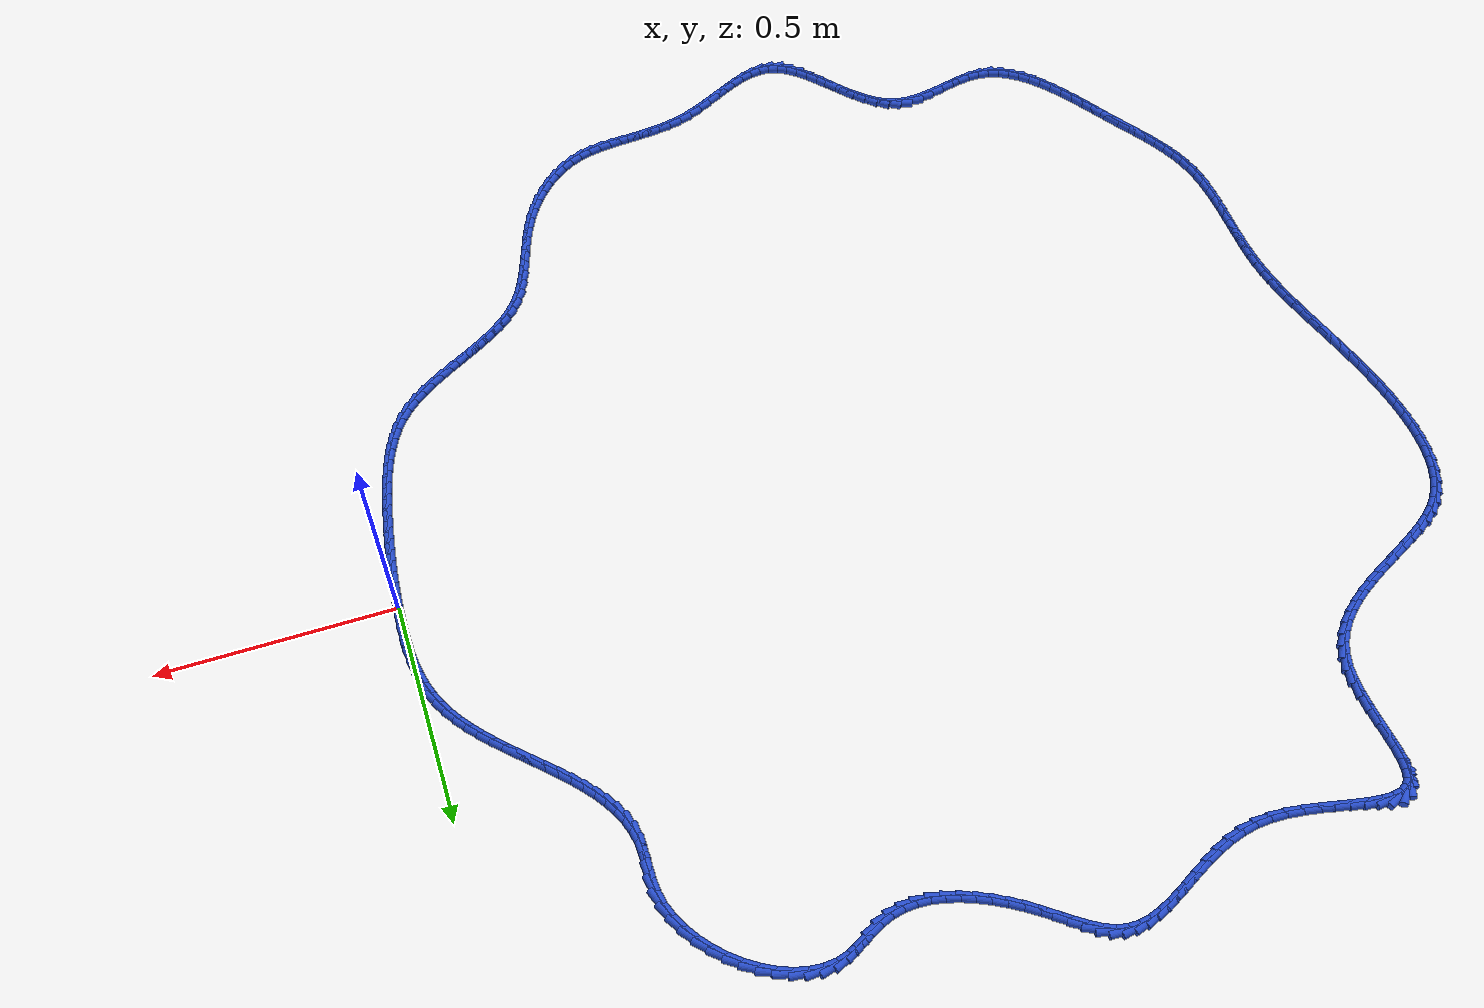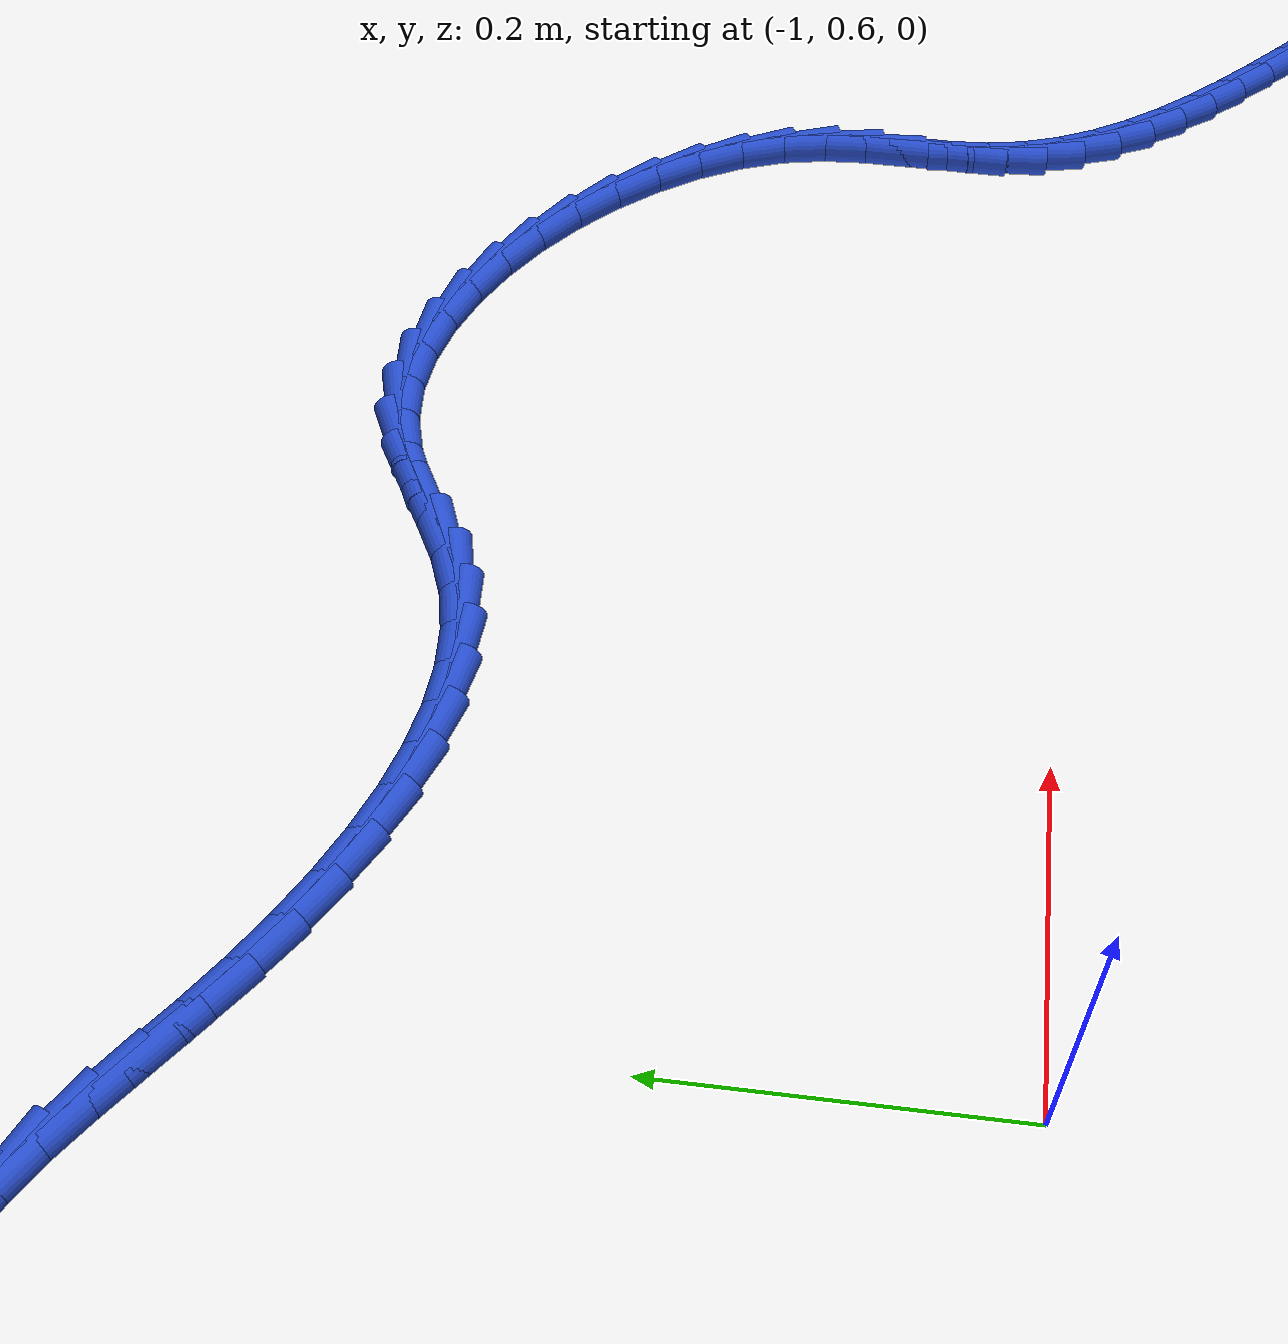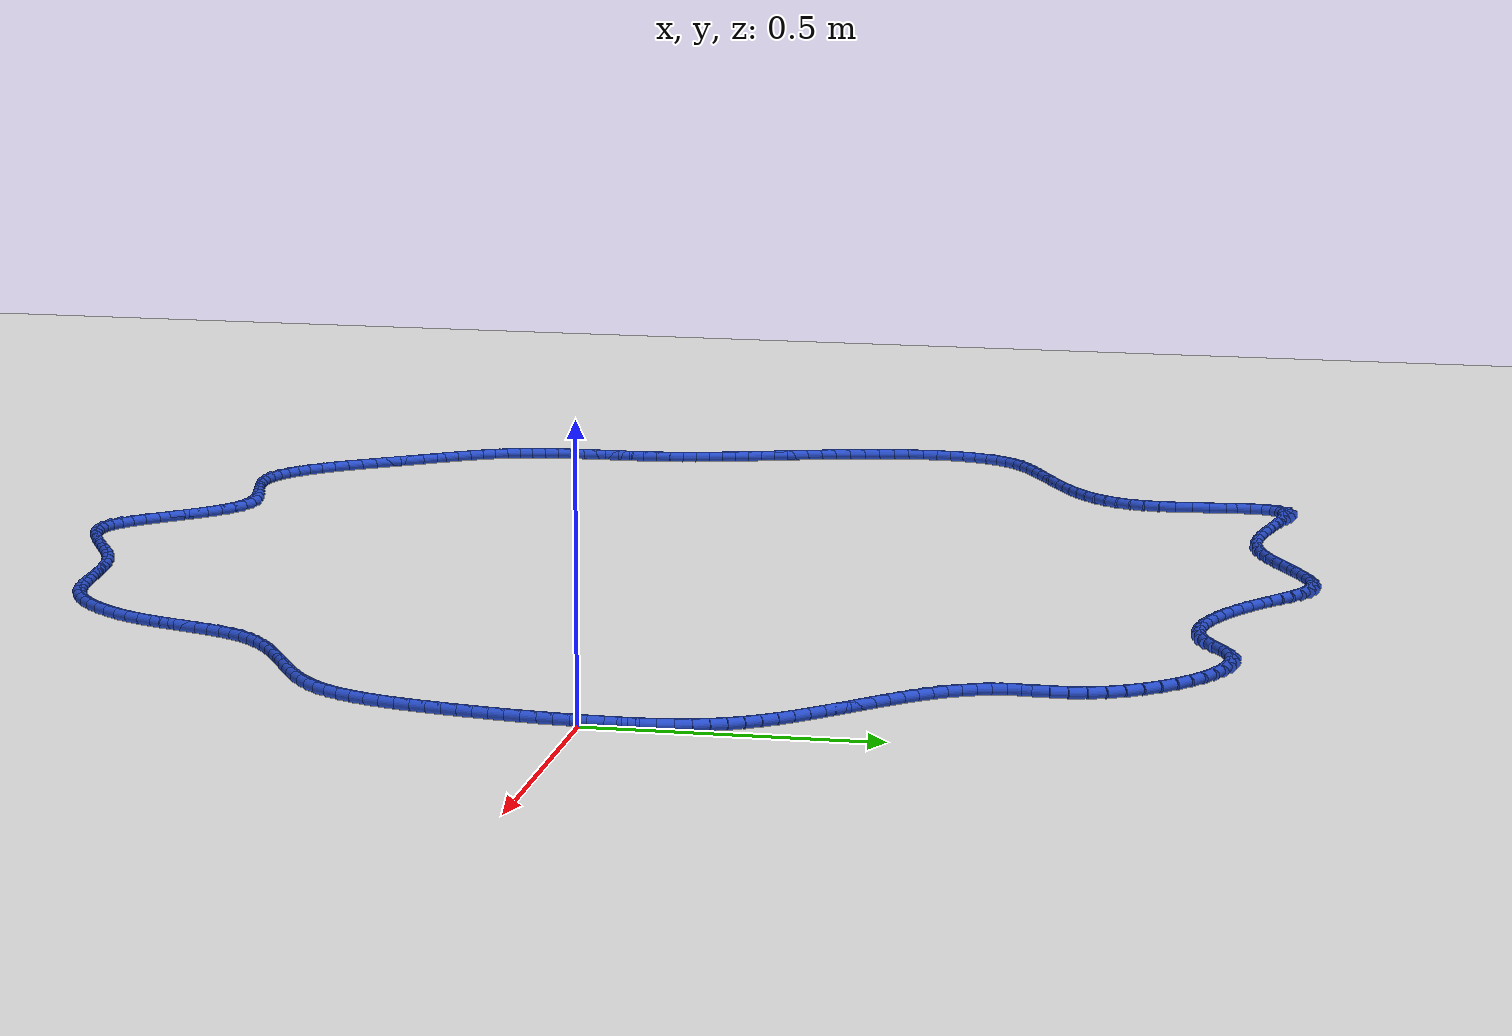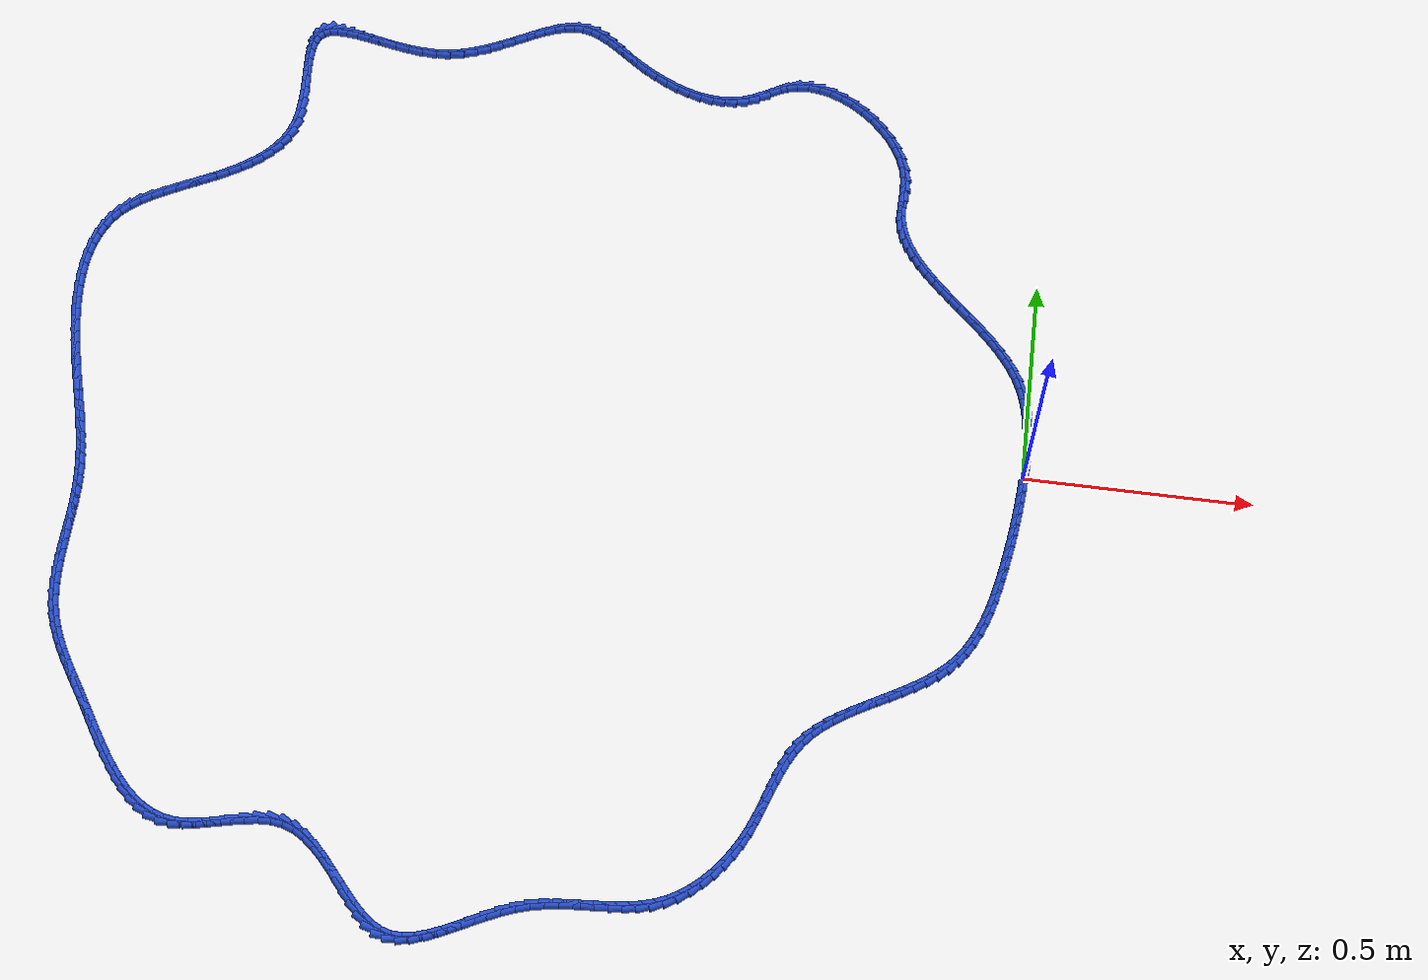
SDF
<sdf version="1.6">
 <world name="default">
  <light name="sun" type="directional">
   <pose>0 0 10 0 -0 0</pose>
   <diffuse>0.8 0.8 0.8 1</diffuse>
   <specular>0.2 0.2 0.2 1</specular>
   <attenuation>
    <range>1000</range>
    <constant>0.9</constant>
    <linear>0.01</linear>
    <quadratic>0.001</quadratic>
   </attenuation>
   <direction>-0.5 0.1 -0.9</direction>
  </light>
  <model name="ground_plane">
   <static>1</static>
   <link name="link">
    <collision name="collision">
     <geometry><plane><normal>0 0 1</normal><size>100 100</size></plane></geometry>
     <surface><friction><ode><mu>100</mu><mu2>50</mu2></ode></friction></surface>
    </collision>
    <visual name="visual">
     <cast_shadows>0</cast_shadows>
     <geometry><plane><normal>0 0 1</normal><size>100 100</size></plane></geometry>
     <material>
      <script><uri>file://media/materials/scripts/gazebo.material</uri><name>Gazebo/WhiteGlow</name></script>
     </material>
    </visual>
   </link>
  </model>
  <gravity>0 0 -9.8</gravity>
  <magnetic_field>6e-06 2.3e-05 -4.2e-05</magnetic_field>
  <atmosphere type="adiabatic"/>
  <physics name="default_physics" default="0" type="ode">
   <max_step_size>0.001</max_step_size>
   <real_time_factor>1</real_time_factor>
   <real_time_update_rate>1000</real_time_update_rate>
  </physics>
  <scene><ambient>0.4 0.4 0.4 1</ambient><background>0.7 0.7 0.7 1</background><shadows>1</shadows></scene>
  <spherical_coordinates>
   <surface_model>EARTH_WGS84</surface_model>
   <latitude_deg>0</latitude_deg>
   <longitude_deg>0</longitude_deg>
   <elevation>0</elevation>
   <heading_deg>0</heading_deg>
  </spherical_coordinates>
  <model name="line">
   <link name="link_0">
    <pose>1.0299920638612292e-18 1.3877787807814457e-17 0.01 0 1.57 1.524596654501401</pose>
    <collision name="collision">
     <geometry><cylinder><radius>0.01</radius><length>0.08</length></cylinder></geometry>
    </collision>
    <visual name="visual">
     <material>
      <script><name>Gazebo/Blue</name><uri>file://media/materials/scripts/gazebo.material</uri></script>
     </material>
     <geometry><cylinder><radius>0.01</radius><length>0.08</length></cylinder></geometry>
    </visual>
   </link>
   <link name="link_1">
    <pose>0.0012995794318501834 0.02810960823162582 0.01 0 1.57 1.5480155194514944</pose>
    <collision name="collision">
     <geometry><cylinder><radius>0.01</radius><length>0.08</length></cylinder></geometry>
    </collision>
    <visual name="visual">
     <material>
      <script><name>Gazebo/Blue</name><uri>file://media/materials/scripts/gazebo.material</uri></script>
     </material>
     <geometry><cylinder><radius>0.01</radius><length>0.08</length></cylinder></geometry>
    </visual>
   </link>
   <link name="link_2">
    <pose>0.0019438009977629273 0.056383852839954396 0.01 0 1.57 -1.5617484835890312</pose>
    <collision name="collision">
     <geometry><cylinder><radius>0.01</radius><length>0.08</length></cylinder></geometry>
    </collision>
    <visual name="visual">
     <material>
      <script><name>Gazebo/Blue</name><uri>file://media/materials/scripts/gazebo.material</uri></script>
     </material>
     <geometry><cylinder><radius>0.01</radius><length>0.08</length></cylinder></geometry>
    </visual>
   </link>
   <link name="link_3">
    <pose>0.0016878100425737725 0.08467611696201711 0.01 0 1.57 -1.5210902962276536</pose>
    <collision name="collision">
     <geometry><cylinder><radius>0.01</radius><length>0.08</length></cylinder></geometry>
    </collision>
    <visual name="visual">
     <material>
      <script><name>Gazebo/Blue</name><uri>file://media/materials/scripts/gazebo.material</uri></script>
     </material>
     <geometry><cylinder><radius>0.01</radius><length>0.08</length></cylinder></geometry>
    </visual>
   </link>
   <link name="link_4">
    <pose>0.000286751911118262 0.11283978373484543 0.01 0 1.57 -1.4710518882741541</pose>
    <collision name="collision">
     <geometry><cylinder><radius>0.01</radius><length>0.08</length></cylinder></geometry>
    </collision>
    <visual name="visual">
     <material>
      <script><name>Gazebo/Blue</name><uri>file://media/materials/scripts/gazebo.material</uri></script>
     </material>
     <geometry><cylinder><radius>0.01</radius><length>0.08</length></cylinder></geometry>
    </visual>
   </link>
   <link name="link_5">
    <pose>-0.0025042280517680662 0.14072823629547068 0.01 0 1.57 -1.411037345589149</pose>
    <collision name="collision">
     <geometry><cylinder><radius>0.01</radius><length>0.08</length></cylinder></geometry>
    </collision>
    <visual name="visual">
     <material>
      <script><name>Gazebo/Blue</name><uri>file://media/materials/scripts/gazebo.material</uri></script>
     </material>
     <geometry><cylinder><radius>0.01</radius><length>0.08</length></cylinder></geometry>
    </visual>
   </link>
   <link name="link_6">
    <pose>-0.006929984501249669 0.1681948577809243 0.01 0 1.57 -1.3405369817601482</pose>
    <collision name="collision">
     <geometry><cylinder><radius>0.01</radius><length>0.08</length></cylinder></geometry>
    </collision>
    <visual name="visual">
     <material>
      <script><name>Gazebo/Blue</name><uri>file://media/materials/scripts/gazebo.material</uri></script>
     </material>
     <geometry><cylinder><radius>0.01</radius><length>0.08</length></cylinder></geometry>
    </visual>
   </link>
   <link name="link_7">
    <pose>-0.013235372092491 0.1950930313282377 0.01 0 1.57 -1.259317850776316</pose>
    <collision name="collision">
     <geometry><cylinder><radius>0.01</radius><length>0.08</length></cylinder></geometry>
    </collision>
    <visual name="visual">
     <material>
      <script><name>Gazebo/Blue</name><uri>file://media/materials/scripts/gazebo.material</uri></script>
     </material>
     <geometry><cylinder><radius>0.01</radius><length>0.08</length></cylinder></geometry>
    </visual>
   </link>
   <link name="link_8">
    <pose>-0.021665245480656528 0.2212761400744422 0.01 0 1.57 -1.1677625449954943</pose>
    <collision name="collision">
     <geometry><cylinder><radius>0.01</radius><length>0.08</length></cylinder></geometry>
    </collision>
    <visual name="visual">
     <material>
      <script><name>Gazebo/Blue</name><uri>file://media/materials/scripts/gazebo.material</uri></script>
     </material>
     <geometry><cylinder><radius>0.01</radius><length>0.08</length></cylinder></geometry>
    </visual>
   </link>
   <link name="link_9">
    <pose>-0.032462093332376284 0.24659862749176453 0.01 0 1.57 -1.0746625207536677</pose>
    <collision name="collision">
     <geometry><cylinder><radius>0.01</radius><length>0.08</length></cylinder></geometry>
    </collision>
    <visual name="visual">
     <material>
      <script><name>Gazebo/Blue</name><uri>file://media/materials/scripts/gazebo.material</uri></script>
     </material>
     <geometry><cylinder><radius>0.01</radius><length>0.08</length></cylinder></geometry>
    </visual>
   </link>
   <link name="link_10">
    <pose>-0.04567198882232284 0.27100296210242103 0.01 0 1.57 -0.994409094864326</pose>
    <collision name="collision">
     <geometry><cylinder><radius>0.01</radius><length>0.08</length></cylinder></geometry>
    </collision>
    <visual name="visual">
     <material>
      <script><name>Gazebo/Blue</name><uri>file://media/materials/scripts/gazebo.material</uri></script>
     </material>
     <geometry><cylinder><radius>0.01</radius><length>0.08</length></cylinder></geometry>
    </visual>
   </link>
   <link name="link_11">
    <pose>-0.06100027106375672 0.29458431490891634 0.01 0 1.57 -0.9282357230222996</pose>
    <collision name="collision">
     <geometry><cylinder><radius>0.01</radius><length>0.08</length></cylinder></geometry>
    </collision>
    <visual name="visual">
     <material>
      <script><name>Gazebo/Blue</name><uri>file://media/materials/scripts/gazebo.material</uri></script>
     </material>
     <geometry><cylinder><radius>0.01</radius><length>0.08</length></cylinder></geometry>
    </visual>
   </link>
   <link name="link_12">
    <pose>-0.07811827432050887 0.3174530964375885 0.01 0 1.57 -0.8754344284416488</pose>
    <collision name="collision">
     <geometry><cylinder><radius>0.01</radius><length>0.08</length></cylinder></geometry>
    </collision>
    <visual name="visual">
     <material>
      <script><name>Gazebo/Blue</name><uri>file://media/materials/scripts/gazebo.material</uri></script>
     </material>
     <geometry><cylinder><radius>0.01</radius><length>0.08</length></cylinder></geometry>
    </visual>
   </link>
   <link name="link_13">
    <pose>-0.09669733285641029 0.33971971721477573 0.01 0 1.57 -0.8350946309687263</pose>
    <collision name="collision">
     <geometry><cylinder><radius>0.01</radius><length>0.08</length></cylinder></geometry>
    </collision>
    <visual name="visual">
     <material>
      <script><name>Gazebo/Blue</name><uri>file://media/materials/scripts/gazebo.material</uri></script>
     </material>
     <geometry><cylinder><radius>0.01</radius><length>0.08</length></cylinder></geometry>
    </visual>
   </link>
   <link name="link_14">
    <pose>-0.11640878093529186 0.36149458776681576 0.01 0 1.57 -0.8063539632807074</pose>
    <collision name="collision">
     <geometry><cylinder><radius>0.01</radius><length>0.08</length></cylinder></geometry>
    </collision>
    <visual name="visual">
     <material>
      <script><name>Gazebo/Blue</name><uri>file://media/materials/scripts/gazebo.material</uri></script>
     </material>
     <geometry><cylinder><radius>0.01</radius><length>0.08</length></cylinder></geometry>
    </visual>
   </link>
   <link name="link_15">
    <pose>-0.13692395282098463 0.38288811862004707 0.01 0 1.57 -0.7885414164947433</pose>
    <collision name="collision">
     <geometry><cylinder><radius>0.01</radius><length>0.08</length></cylinder></geometry>
    </collision>
    <visual name="visual">
     <material>
      <script><name>Gazebo/Blue</name><uri>file://media/materials/scripts/gazebo.material</uri></script>
     </material>
     <geometry><cylinder><radius>0.01</radius><length>0.08</length></cylinder></geometry>
    </visual>
   </link>
   <link name="link_16">
    <pose>-0.15791418277731945 0.4040107203008073 0.01 0 1.57 -0.7812522340916915</pose>
    <collision name="collision">
     <geometry><cylinder><radius>0.01</radius><length>0.08</length></cylinder></geometry>
    </collision>
    <visual name="visual">
     <material>
      <script><name>Gazebo/Blue</name><uri>file://media/materials/scripts/gazebo.material</uri></script>
     </material>
     <geometry><cylinder><radius>0.01</radius><length>0.08</length></cylinder></geometry>
    </visual>
   </link>
   <link name="link_17">
    <pose>-0.17905080506812737 0.4249728033354349 0.01 0 1.57 -0.7843860382343165</pose>
    <collision name="collision">
     <geometry><cylinder><radius>0.01</radius><length>0.08</length></cylinder></geometry>
    </collision>
    <visual name="visual">
     <material>
      <script><name>Gazebo/Blue</name><uri>file://media/materials/scripts/gazebo.material</uri></script>
     </material>
     <geometry><cylinder><radius>0.01</radius><length>0.08</length></cylinder></geometry>
    </visual>
   </link>
   <link name="link_18">
    <pose>-0.20000515395723936 0.44588477825026784 0.01 0 1.57 -0.7981672097057642</pose>
    <collision name="collision">
     <geometry><cylinder><radius>0.01</radius><length>0.08</length></cylinder></geometry>
    </collision>
    <visual name="visual">
     <material>
      <script><name>Gazebo/Blue</name><uri>file://media/materials/scripts/gazebo.material</uri></script>
     </material>
     <geometry><cylinder><radius>0.01</radius><length>0.08</length></cylinder></geometry>
    </visual>
   </link>
   <link name="link_19">
    <pose>-0.2204485637084863 0.466857055571644 0.01 0 1.57 -0.8231546030872825</pose>
    <collision name="collision">
     <geometry><cylinder><radius>0.01</radius><length>0.08</length></cylinder></geometry>
    </collision>
    <visual name="visual">
     <material>
      <script><name>Gazebo/Blue</name><uri>file://media/materials/scripts/gazebo.material</uri></script>
     </material>
     <geometry><cylinder><radius>0.01</radius><length>0.08</length></cylinder></geometry>
    </visual>
   </link>
   <link name="link_20">
    <pose>-0.24005236858569914 0.4880000458259015 0.01 0 1.57 -0.8602357040350318</pose>
    <collision name="collision">
     <geometry><cylinder><radius>0.01</radius><length>0.08</length></cylinder></geometry>
    </collision>
    <visual name="visual">
     <material>
      <script><name>Gazebo/Blue</name><uri>file://media/materials/scripts/gazebo.material</uri></script>
     </material>
     <geometry><cylinder><radius>0.01</radius><length>0.08</length></cylinder></geometry>
    </visual>
   </link>
   <link name="link_21">
    <pose>-0.25848790285270895 0.5094241595393786 0.01 0 1.57 -0.9105856234175619</pose>
    <collision name="collision">
     <geometry><cylinder><radius>0.01</radius><length>0.08</length></cylinder></geometry>
    </collision>
    <visual name="visual">
     <material>
      <script><name>Gazebo/Blue</name><uri>file://media/materials/scripts/gazebo.material</uri></script>
     </material>
     <geometry><cylinder><radius>0.01</radius><length>0.08</length></cylinder></geometry>
    </visual>
   </link>
   <link name="link_22">
    <pose>-0.2754265007733465 0.531239807238413 0.01 0 1.57 -0.9755514953426091</pose>
    <collision name="collision">
     <geometry><cylinder><radius>0.01</radius><length>0.08</length></cylinder></geometry>
    </collision>
    <visual name="visual">
     <material>
      <script><name>Gazebo/Blue</name><uri>file://media/materials/scripts/gazebo.material</uri></script>
     </material>
     <geometry><cylinder><radius>0.01</radius><length>0.08</length></cylinder></geometry>
    </visual>
   </link>
   <link name="link_23">
    <pose>-0.290539496611443 0.5535573994493432 0.01 0 1.57 -1.0564004418718724</pose>
    <collision name="collision">
     <geometry><cylinder><radius>0.01</radius><length>0.08</length></cylinder></geometry>
    </collision>
    <visual name="visual">
     <material>
      <script><name>Gazebo/Blue</name><uri>file://media/materials/scripts/gazebo.material</uri></script>
     </material>
     <geometry><cylinder><radius>0.01</radius><length>0.08</length></cylinder></geometry>
    </visual>
   </link>
   <link name="link_24">
    <pose>-0.3034982246308293 0.5764873466985071 0.01 0 1.57 -1.1538621455678169</pose>
    <collision name="collision">
     <geometry><cylinder><radius>0.01</radius><length>0.08</length></cylinder></geometry>
    </collision>
    <visual name="visual">
     <material>
      <script><name>Gazebo/Blue</name><uri>file://media/materials/scripts/gazebo.material</uri></script>
     </material>
     <geometry><cylinder><radius>0.01</radius><length>0.08</length></cylinder></geometry>
    </visual>
   </link>
   <link name="link_25">
    <pose>-0.31397401909533607 0.6001400595122424 0.01 0 1.57 -1.2674518433417834</pose>
    <collision name="collision">
     <geometry><cylinder><radius>0.01</radius><length>0.08</length></cylinder></geometry>
    </collision>
    <visual name="visual">
     <material>
      <script><name>Gazebo/Blue</name><uri>file://media/materials/scripts/gazebo.material</uri></script>
     </material>
     <geometry><cylinder><radius>0.01</radius><length>0.08</length></cylinder></geometry>
    </visual>
   </link>
   <link name="link_26">
    <pose>-0.3216382142687949 0.6246259484168879 0.01 0 1.57 -1.3947372178408934</pose>
    <collision name="collision">
     <geometry><cylinder><radius>0.01</radius><length>0.08</length></cylinder></geometry>
    </collision>
    <visual name="visual">
     <material>
      <script><name>Gazebo/Blue</name><uri>file://media/materials/scripts/gazebo.material</uri></script>
     </material>
     <geometry><cylinder><radius>0.01</radius><length>0.08</length></cylinder></geometry>
    </visual>
   </link>
   <link name="link_27">
    <pose>-0.326162144415036 0.6500554239387806 0.01 0 1.57 -1.5211517138171886</pose>
    <collision name="collision">
     <geometry><cylinder><radius>0.01</radius><length>0.08</length></cylinder></geometry>
    </collision>
    <visual name="visual">
     <material>
      <script><name>Gazebo/Blue</name><uri>file://media/materials/scripts/gazebo.material</uri></script>
     </material>
     <geometry><cylinder><radius>0.01</radius><length>0.08</length></cylinder></geometry>
    </visual>
   </link>
   <link name="link_28">
    <pose>-0.32747609507731223 0.6765008116111341 0.01 0 1.57 1.5525218159534144</pose>
    <collision name="collision">
     <geometry><cylinder><radius>0.01</radius><length>0.08</length></cylinder></geometry>
    </collision>
    <visual name="visual">
     <material>
      <script><name>Gazebo/Blue</name><uri>file://media/materials/scripts/gazebo.material</uri></script>
     </material>
     <geometry><cylinder><radius>0.01</radius><length>0.08</length></cylinder></geometry>
    </visual>
   </link>
   <link name="link_29">
    <pose>-0.3269768173885187 0.7038187580486174 0.01 0 1.57 1.556492656625533</pose>
    <collision name="collision">
     <geometry><cylinder><radius>0.01</radius><length>0.08</length></cylinder></geometry>
    </collision>
    <visual name="visual">
     <material>
      <script><name>Gazebo/Blue</name><uri>file://media/materials/scripts/gazebo.material</uri></script>
     </material>
     <geometry><cylinder><radius>0.01</radius><length>0.08</length></cylinder></geometry>
    </visual>
   </link>
   <link name="link_30">
    <pose>-0.3265766976322833 0.7317900733563658 0.01 0 1.57 -1.5141076287134394</pose>
    <collision name="collision">
     <geometry><cylinder><radius>0.01</radius><length>0.08</length></cylinder></geometry>
    </collision>
    <visual name="visual">
     <material>
      <script><name>Gazebo/Blue</name><uri>file://media/materials/scripts/gazebo.material</uri></script>
     </material>
     <geometry><cylinder><radius>0.01</radius><length>0.08</length></cylinder></geometry>
    </visual>
   </link>
   <link name="link_31">
    <pose>-0.3281886905237016 0.76019548403804 0.01 0 1.57 -1.3827110717498414</pose>
    <collision name="collision">
     <geometry><cylinder><radius>0.01</radius><length>0.08</length></cylinder></geometry>
    </collision>
    <visual name="visual">
     <material>
      <script><name>Gazebo/Blue</name><uri>file://media/materials/scripts/gazebo.material</uri></script>
     </material>
     <geometry><cylinder><radius>0.01</radius><length>0.08</length></cylinder></geometry>
    </visual>
   </link>
   <link name="link_32">
    <pose>-0.3336345044622485 0.7888072155773351 0.01 0 1.57 -1.2391757874583416</pose>
    <collision name="collision">
     <geometry><cylinder><radius>0.01</radius><length>0.08</length></cylinder></geometry>
    </collision>
    <visual name="visual">
     <material>
      <script><name>Gazebo/Blue</name><uri>file://media/materials/scripts/gazebo.material</uri></script>
     </material>
     <geometry><cylinder><radius>0.01</radius><length>0.08</length></cylinder></geometry>
    </visual>
   </link>
   <link name="link_33">
    <pose>-0.3434375314384174 0.8172765349990724 0.01 0 1.57 -1.113672842559572</pose>
    <collision name="collision">
     <geometry><cylinder><radius>0.01</radius><length>0.08</length></cylinder></geometry>
    </collision>
    <visual name="visual">
     <material>
      <script><name>Gazebo/Blue</name><uri>file://media/materials/scripts/gazebo.material</uri></script>
     </material>
     <geometry><cylinder><radius>0.01</radius><length>0.08</length></cylinder></geometry>
    </visual>
   </link>
   <link name="link_34">
    <pose>-0.35715491193405224 0.8451646879029725 0.01 0 1.57 -1.0022342994812339</pose>
    <collision name="collision">
     <geometry><cylinder><radius>0.01</radius><length>0.08</length></cylinder></geometry>
    </collision>
    <visual name="visual">
     <material>
      <script><name>Gazebo/Blue</name><uri>file://media/materials/scripts/gazebo.material</uri></script>
     </material>
     <geometry><cylinder><radius>0.01</radius><length>0.08</length></cylinder></geometry>
    </visual>
   </link>
   <link name="link_35">
    <pose>-0.3743207750932368 0.8720307760231042 0.01 0 1.57 -0.9002465234506688</pose>
    <collision name="collision">
     <geometry><cylinder><radius>0.01</radius><length>0.08</length></cylinder></geometry>
    </collision>
    <visual name="visual">
     <material>
      <script><name>Gazebo/Blue</name><uri>file://media/materials/scripts/gazebo.material</uri></script>
     </material>
     <geometry><cylinder><radius>0.01</radius><length>0.08</length></cylinder></geometry>
    </visual>
   </link>
   <link name="link_36">
    <pose>-0.3944692500600547 0.8974339010935373 0.01 0 1.57 -0.8034630720071869</pose>
    <collision name="collision">
     <geometry><cylinder><radius>0.01</radius><length>0.08</length></cylinder></geometry>
    </collision>
    <visual name="visual">
     <material>
      <script><name>Gazebo/Blue</name><uri>file://media/materials/scripts/gazebo.material</uri></script>
     </material>
     <geometry><cylinder><radius>0.01</radius><length>0.08</length></cylinder></geometry>
    </visual>
   </link>
   <link name="link_37">
    <pose>-0.41713446597858994 0.9209331648483418 0.01 0 1.57 -0.7079095050951352</pose>
    <collision name="collision">
     <geometry><cylinder><radius>0.01</radius><length>0.08</length></cylinder></geometry>
    </collision>
    <visual name="visual">
     <material>
      <script><name>Gazebo/Blue</name><uri>file://media/materials/scripts/gazebo.material</uri></script>
     </material>
     <geometry><cylinder><radius>0.01</radius><length>0.08</length></cylinder></geometry>
    </visual>
   </link>
   <link name="link_38">
    <pose>-0.4418505519929266 0.9420876690215872 0.01 0 1.57 -0.6096556347336491</pose>
    <collision name="collision">
     <geometry><cylinder><radius>0.01</radius><length>0.08</length></cylinder></geometry>
    </collision>
    <visual name="visual">
     <material>
      <script><name>Gazebo/Blue</name><uri>file://media/materials/scripts/gazebo.material</uri></script>
     </material>
     <geometry><cylinder><radius>0.01</radius><length>0.08</length></cylinder></geometry>
    </visual>
   </link>
   <link name="link_39">
    <pose>-0.46815163724714814 0.9604565153473433 0.01 0 1.57 -0.5045544071287962</pose>
    <collision name="collision">
     <geometry><cylinder><radius>0.01</radius><length>0.08</length></cylinder></geometry>
    </collision>
    <visual name="visual">
     <material>
      <script><name>Gazebo/Blue</name><uri>file://media/materials/scripts/gazebo.material</uri></script>
     </material>
     <geometry><cylinder><radius>0.01</radius><length>0.08</length></cylinder></geometry>
    </visual>
   </link>
   <link name="link_40">
    <pose>-0.49557185088533834 0.9755988055596796 0.01 0 1.57 -0.38802068075002644</pose>
    <collision name="collision">
     <geometry><cylinder><radius>0.01</radius><length>0.08</length></cylinder></geometry>
    </collision>
    <visual name="visual">
     <material>
      <script><name>Gazebo/Blue</name><uri>file://media/materials/scripts/gazebo.material</uri></script>
     </material>
     <geometry><cylinder><radius>0.01</radius><length>0.08</length></cylinder></geometry>
    </visual>
   </link>
   <link name="link_41">
    <pose>-0.5236453220515811 0.9870736413926657 0.01 0 1.57 -0.25498643271261234</pose>
    <collision name="collision">
     <geometry><cylinder><radius>0.01</radius><length>0.08</length></cylinder></geometry>
    </collision>
    <visual name="visual">
     <material>
      <script><name>Gazebo/Blue</name><uri>file://media/materials/scripts/gazebo.material</uri></script>
     </material>
     <geometry><cylinder><radius>0.01</radius><length>0.08</length></cylinder></geometry>
    </visual>
   </link>
   <link name="link_42">
    <pose>-0.5519061798899605 0.9944401245803717 0.01 0 1.57 -0.10034070326478406</pose>
    <collision name="collision">
     <geometry><cylinder><radius>0.01</radius><length>0.08</length></cylinder></geometry>
    </collision>
    <visual name="visual">
     <material>
      <script><name>Gazebo/Blue</name><uri>file://media/materials/scripts/gazebo.material</uri></script>
     </material>
     <geometry><cylinder><radius>0.01</radius><length>0.08</length></cylinder></geometry>
    </visual>
   </link>
   <link name="link_43">
    <pose>-0.5798885535445601 0.9972573568568668 0.01 0 1.57 0.07960655723129907</pose>
    <collision name="collision">
     <geometry><cylinder><radius>0.01</radius><length>0.08</length></cylinder></geometry>
    </collision>
    <visual name="visual">
     <material>
      <script><name>Gazebo/Blue</name><uri>file://media/materials/scripts/gazebo.material</uri></script>
     </material>
     <geometry><cylinder><radius>0.01</radius><length>0.08</length></cylinder></geometry>
    </visual>
   </link>
   <link name="link_44">
    <pose>-0.6071265721594638 0.9950844399562211 0.01 0 1.57 0.2834193827274493</pose>
    <collision name="collision">
     <geometry><cylinder><radius>0.01</radius><length>0.08</length></cylinder></geometry>
    </collision>
    <visual name="visual">
     <material>
      <script><name>Gazebo/Blue</name><uri>file://media/materials/scripts/gazebo.material</uri></script>
     </material>
     <geometry><cylinder><radius>0.01</radius><length>0.08</length></cylinder></geometry>
    </visual>
   </link>
   <link name="link_45">
    <pose>-0.6331618707111839 0.9875013961187414 0.01 0 1.57 0.4573855697178765</pose>
    <collision name="collision">
     <geometry><cylinder><radius>0.01</radius><length>0.08</length></cylinder></geometry>
    </collision>
    <visual name="visual">
     <material>
      <script><name>Gazebo/Blue</name><uri>file://media/materials/scripts/gazebo.material</uri></script>
     </material>
     <geometry><cylinder><radius>0.01</radius><length>0.08</length></cylinder></geometry>
    </visual>
   </link>
   <link name="link_46">
    <pose>-0.6579679394331743 0.9752919289461995 0.01 0 1.57 0.530949737364162</pose>
    <collision name="collision">
     <geometry><cylinder><radius>0.01</radius><length>0.08</length></cylinder></geometry>
    </collision>
    <visual name="visual">
     <material>
      <script><name>Gazebo/Blue</name><uri>file://media/materials/scripts/gazebo.material</uri></script>
     </material>
     <geometry><cylinder><radius>0.01</radius><length>0.08</length></cylinder></geometry>
    </visual>
   </link>
   <link name="link_47">
    <pose>-0.6821772209483101 0.961076396096303 0.01 0 1.57 0.505410260540674</pose>
    <collision name="collision">
     <geometry><cylinder><radius>0.01</radius><length>0.08</length></cylinder></geometry>
    </collision>
    <visual name="visual">
     <material>
      <script><name>Gazebo/Blue</name><uri>file://media/materials/scripts/gazebo.material</uri></script>
     </material>
     <geometry><cylinder><radius>0.01</radius><length>0.08</length></cylinder></geometry>
    </visual>
   </link>
   <link name="link_48">
    <pose>-0.7064776409796532 0.9476297995722853 0.01 0 1.57 0.381087394276146</pose>
    <collision name="collision">
     <geometry><cylinder><radius>0.01</radius><length>0.08</length></cylinder></geometry>
    </collision>
    <visual name="visual">
     <material>
      <script><name>Gazebo/Blue</name><uri>file://media/materials/scripts/gazebo.material</uri></script>
     </material>
     <geometry><cylinder><radius>0.01</radius><length>0.08</length></cylinder></geometry>
    </visual>
   </link>
   <link name="link_49">
    <pose>-0.7315201335684859 0.9375959204744445 0.01 0 1.57 0.21675197105116678</pose>
    <collision name="collision">
     <geometry><cylinder><radius>0.01</radius><length>0.08</length></cylinder></geometry>
    </collision>
    <visual name="visual">
     <material>
      <script><name>Gazebo/Blue</name><uri>file://media/materials/scripts/gazebo.material</uri></script>
     </material>
     <geometry><cylinder><radius>0.01</radius><length>0.08</length></cylinder></geometry>
    </visual>
   </link>
   <link name="link_50">
    <pose>-0.7574661811389911 0.9318823040779112 0.01 0 1.57 0.06422622571828837</pose>
    <collision name="collision">
     <geometry><cylinder><radius>0.01</radius><length>0.08</length></cylinder></geometry>
    </collision>
    <visual name="visual">
     <material>
      <script><name>Gazebo/Blue</name><uri>file://media/materials/scripts/gazebo.material</uri></script>
     </material>
     <geometry><cylinder><radius>0.01</radius><length>0.08</length></cylinder></geometry>
    </visual>
   </link>
   <link name="link_51">
    <pose>-0.7841307734382874 0.9301673792792858 0.01 0 1.57 -0.07108819385184693</pose>
    <collision name="collision">
     <geometry><cylinder><radius>0.01</radius><length>0.08</length></cylinder></geometry>
    </collision>
    <visual name="visual">
     <material>
      <script><name>Gazebo/Blue</name><uri>file://media/materials/scripts/gazebo.material</uri></script>
     </material>
     <geometry><cylinder><radius>0.01</radius><length>0.08</length></cylinder></geometry>
    </visual>
   </link>
   <link name="link_52">
    <pose>-0.8113215740590275 0.9321035868460066 0.01 0 1.57 -0.1881158327605718</pose>
    <collision name="collision">
     <geometry><cylinder><radius>0.01</radius><length>0.08</length></cylinder></geometry>
    </collision>
    <visual name="visual">
     <material>
      <script><name>Gazebo/Blue</name><uri>file://media/materials/scripts/gazebo.material</uri></script>
     </material>
     <geometry><cylinder><radius>0.01</radius><length>0.08</length></cylinder></geometry>
    </visual>
   </link>
   <link name="link_53">
    <pose>-0.8388462465938653 0.9373433675455118 0.01 0 1.57 -0.2880022688724127</pose>
    <collision name="collision">
     <geometry><cylinder><radius>0.01</radius><length>0.08</length></cylinder></geometry>
    </collision>
    <visual name="visual">
     <material>
      <script><name>Gazebo/Blue</name><uri>file://media/materials/scripts/gazebo.material</uri></script>
     </material>
     <geometry><cylinder><radius>0.01</radius><length>0.08</length></cylinder></geometry>
    </visual>
   </link>
   <link name="link_54">
    <pose>-0.8665124546354538 0.945539162145239 0.01 0 1.57 -0.37293183494573295</pose>
    <collision name="collision">
     <geometry><cylinder><radius>0.01</radius><length>0.08</length></cylinder></geometry>
    </collision>
    <visual name="visual">
     <material>
      <script><name>Gazebo/Blue</name><uri>file://media/materials/scripts/gazebo.material</uri></script>
     </material>
     <geometry><cylinder><radius>0.01</radius><length>0.08</length></cylinder></geometry>
    </visual>
   </link>
   <link name="link_55">
    <pose>-0.8941278617764461 0.9563434114126266 0.01 0 1.57 -0.44533397743568104</pose>
    <collision name="collision">
     <geometry><cylinder><radius>0.01</radius><length>0.08</length></cylinder></geometry>
    </collision>
    <visual name="visual">
     <material>
      <script><name>Gazebo/Blue</name><uri>file://media/materials/scripts/gazebo.material</uri></script>
     </material>
     <geometry><cylinder><radius>0.01</radius><length>0.08</length></cylinder></geometry>
    </visual>
   </link>
   <link name="link_56">
    <pose>-0.9215001316094951 0.969408556115112 0.01 0 1.57 -0.5074840652584793</pose>
    <collision name="collision">
     <geometry><cylinder><radius>0.01</radius><length>0.08</length></cylinder></geometry>
    </collision>
    <visual name="visual">
     <material>
      <script><name>Gazebo/Blue</name><uri>file://media/materials/scripts/gazebo.material</uri></script>
     </material>
     <geometry><cylinder><radius>0.01</radius><length>0.08</length></cylinder></geometry>
    </visual>
   </link>
   <link name="link_57">
    <pose>-0.948436927727254 0.9843870370201335 0.01 0 1.57 -0.5613590349849608</pose>
    <collision name="collision">
     <geometry><cylinder><radius>0.01</radius><length>0.08</length></cylinder></geometry>
    </collision>
    <visual name="visual">
     <material>
      <script><name>Gazebo/Blue</name><uri>file://media/materials/scripts/gazebo.material</uri></script>
     </material>
     <geometry><cylinder><radius>0.01</radius><length>0.08</length></cylinder></geometry>
    </visual>
   </link>
   <link name="link_58">
    <pose>-0.9747459137223766 1.0009312948951292 0.01 0 1.57 -0.6086189616180934</pose>
    <collision name="collision">
     <geometry><cylinder><radius>0.01</radius><length>0.08</length></cylinder></geometry>
    </collision>
    <visual name="visual">
     <material>
      <script><name>Gazebo/Blue</name><uri>file://media/materials/scripts/gazebo.material</uri></script>
     </material>
     <geometry><cylinder><radius>0.01</radius><length>0.08</length></cylinder></geometry>
    </visual>
   </link>
   <link name="link_59">
    <pose>-1.0002348231963687 1.0186936285054902 0.01 0 1.57 -0.6443190302506676</pose>
    <collision name="collision">
     <geometry><cylinder><radius>0.01</radius><length>0.08</length></cylinder></geometry>
    </collision>
    <visual name="visual">
     <material>
      <script><name>Gazebo/Blue</name><uri>file://media/materials/scripts/gazebo.material</uri></script>
     </material>
     <geometry><cylinder><radius>0.01</radius><length>0.08</length></cylinder></geometry>
    </visual>
   </link>
   <link name="link_60">
    <pose>-1.0247991652824797 1.0371482976319577 0.01 0 1.57 -0.6501810663338972</pose>
    <collision name="collision">
     <geometry><cylinder><radius>0.01</radius><length>0.08</length></cylinder></geometry>
    </collision>
    <visual name="visual">
     <material>
      <script><name>Gazebo/Blue</name><uri>file://media/materials/scripts/gazebo.material</uri></script>
     </material>
     <geometry><cylinder><radius>0.01</radius><length>0.08</length></cylinder></geometry>
    </visual>
   </link>
   <link name="link_61">
    <pose>-1.0485936660263524 1.0552437809523874 0.01 0 1.57 -0.6201773716894817</pose>
    <collision name="collision">
     <geometry><cylinder><radius>0.01</radius><length>0.08</length></cylinder></geometry>
    </collision>
    <visual name="visual">
     <material>
      <script><name>Gazebo/Blue</name><uri>file://media/materials/scripts/gazebo.material</uri></script>
     </material>
     <geometry><cylinder><radius>0.01</radius><length>0.08</length></cylinder></geometry>
    </visual>
   </link>
   <link name="link_62">
    <pose>-1.071820670645292 1.0718319690772693 0.01 0 1.57 -0.5473271670408135</pose>
    <collision name="collision">
     <geometry><cylinder><radius>0.01</radius><length>0.08</length></cylinder></geometry>
    </collision>
    <visual name="visual">
     <material>
      <script><name>Gazebo/Blue</name><uri>file://media/materials/scripts/gazebo.material</uri></script>
     </material>
     <geometry><cylinder><radius>0.01</radius><length>0.08</length></cylinder></geometry>
    </visual>
   </link>
   <link name="link_63">
    <pose>-1.094682524356604 1.085764752617094 0.01 0 1.57 -0.41972441520622644</pose>
    <collision name="collision">
     <geometry><cylinder><radius>0.01</radius><length>0.08</length></cylinder></geometry>
    </collision>
    <visual name="visual">
     <material>
      <script><name>Gazebo/Blue</name><uri>file://media/materials/scripts/gazebo.material</uri></script>
     </material>
     <geometry><cylinder><radius>0.01</radius><length>0.08</length></cylinder></geometry>
    </visual>
   </link>
   <link name="link_64">
    <pose>-1.117381572377595 1.095894022182351 0.01 0 1.57 -0.22615706002265334</pose>
    <collision name="collision">
     <geometry><cylinder><radius>0.01</radius><length>0.08</length></cylinder></geometry>
    </collision>
    <visual name="visual">
     <material>
      <script><name>Gazebo/Blue</name><uri>file://media/materials/scripts/gazebo.material</uri></script>
     </material>
     <geometry><cylinder><radius>0.01</radius><length>0.08</length></cylinder></geometry>
    </visual>
   </link>
   <link name="link_65">
    <pose>-1.1401170359788912 1.1011253015000118 0.01 0 1.57 -0.009062266083104282</pose>
    <collision name="collision">
     <geometry><cylinder><radius>0.01</radius><length>0.08</length></cylinder></geometry>
    </collision>
    <visual name="visual">
     <material>
      <script><name>Gazebo/Blue</name><uri>file://media/materials/scripts/gazebo.material</uri></script>
     </material>
     <geometry><cylinder><radius>0.01</radius><length>0.08</length></cylinder></geometry>
    </visual>
   </link>
   <link name="link_66">
    <pose>-1.1630317041132896 1.1013329660046756 0.01 0 1.57 0.17502257249680594</pose>
    <collision name="collision">
     <geometry><cylinder><radius>0.01</radius><length>0.08</length></cylinder></geometry>
    </collision>
    <visual name="visual">
     <material>
      <script><name>Gazebo/Blue</name><uri>file://media/materials/scripts/gazebo.material</uri></script>
     </material>
     <geometry><cylinder><radius>0.01</radius><length>0.08</length></cylinder></geometry>
    </visual>
   </link>
   <link name="link_67">
    <pose>-1.1862193653863622 1.097232647912709 0.01 0 1.57 0.3146177550678856</pose>
    <collision name="collision">
     <geometry><cylinder><radius>0.01</radius><length>0.08</length></cylinder></geometry>
    </collision>
    <visual name="visual">
     <material>
      <script><name>Gazebo/Blue</name><uri>file://media/materials/scripts/gazebo.material</uri></script>
     </material>
     <geometry><cylinder><radius>0.01</radius><length>0.08</length></cylinder></geometry>
    </visual>
   </link>
   <link name="link_68">
    <pose>-1.209772180149117 1.0895679339401911 0.01 0 1.57 0.4117492616157398</pose>
    <collision name="collision">
     <geometry><cylinder><radius>0.01</radius><length>0.08</length></cylinder></geometry>
    </collision>
    <visual name="visual">
     <material>
      <script><name>Gazebo/Blue</name><uri>file://media/materials/scripts/gazebo.material</uri></script>
     </material>
     <geometry><cylinder><radius>0.01</radius><length>0.08</length></cylinder></geometry>
    </visual>
   </link>
   <link name="link_69">
    <pose>-1.2337823087525646 1.0790824108032004 0.01 0 1.57 0.47282164596187476</pose>
    <collision name="collision">
     <geometry><cylinder><radius>0.01</radius><length>0.08</length></cylinder></geometry>
    </collision>
    <visual name="visual">
     <material>
      <script><name>Gazebo/Blue</name><uri>file://media/materials/scripts/gazebo.material</uri></script>
     </material>
     <geometry><cylinder><radius>0.01</radius><length>0.08</length></cylinder></geometry>
    </visual>
   </link>
   <link name="link_70">
    <pose>-1.2583419115477146 1.0665196652178164 0.01 0 1.57 0.5039301826507105</pose>
    <collision name="collision">
     <geometry><cylinder><radius>0.01</radius><length>0.08</length></cylinder></geometry>
    </collision>
    <visual name="visual">
     <material>
      <script><name>Gazebo/Blue</name><uri>file://media/materials/scripts/gazebo.material</uri></script>
     </material>
     <geometry><cylinder><radius>0.01</radius><length>0.08</length></cylinder></geometry>
    </visual>
   </link>
   <link name="link_71">
    <pose>-1.2835431488855755 1.0526232839001173 0.01 0 1.57 0.5093960897733321</pose>
    <collision name="collision">
     <geometry><cylinder><radius>0.01</radius><length>0.08</length></cylinder></geometry>
    </collision>
    <visual name="visual">
     <material>
      <script><name>Gazebo/Blue</name><uri>file://media/materials/scripts/gazebo.material</uri></script>
     </material>
     <geometry><cylinder><radius>0.01</radius><length>0.08</length></cylinder></geometry>
    </visual>
   </link>
   <link name="link_72">
    <pose>-1.3094781811171576 1.0381368535661823 0.01 0 1.57 0.4917118843898677</pose>
    <collision name="collision">
     <geometry><cylinder><radius>0.01</radius><length>0.08</length></cylinder></geometry>
    </collision>
    <visual name="visual">
     <material>
      <script><name>Gazebo/Blue</name><uri>file://media/materials/scripts/gazebo.material</uri></script>
     </material>
     <geometry><cylinder><radius>0.01</radius><length>0.08</length></cylinder></geometry>
    </visual>
   </link>
   <link name="link_73">
    <pose>-1.3362391685934703 1.0238039609320906 0.01 0 1.57 0.45190923290805957</pose>
    <collision name="collision">
     <geometry><cylinder><radius>0.01</radius><length>0.08</length></cylinder></geometry>
    </collision>
    <visual name="visual">
     <material>
      <script><name>Gazebo/Blue</name><uri>file://media/materials/scripts/gazebo.material</uri></script>
     </material>
     <geometry><cylinder><radius>0.01</radius><length>0.08</length></cylinder></geometry>
    </visual>
   </link>
   <link name="link_74">
    <pose>-1.3639182716655236 1.0103681927139208 0.01 0 1.57 0.3900640121930981</pose>
    <collision name="collision">
     <geometry><cylinder><radius>0.01</radius><length>0.08</length></cylinder></geometry>
    </collision>
    <visual name="visual">
     <material>
      <script><name>Gazebo/Blue</name><uri>file://media/materials/scripts/gazebo.material</uri></script>
     </material>
     <geometry><cylinder><radius>0.01</radius><length>0.08</length></cylinder></geometry>
    </visual>
   </link>
   <link name="link_75">
    <pose>-1.3926076506843263 0.9985731356277512 0.01 0 1.57 0.305964867944985</pose>
    <collision name="collision">
     <geometry><cylinder><radius>0.01</radius><length>0.08</length></cylinder></geometry>
    </collision>
    <visual name="visual">
     <material>
      <script><name>Gazebo/Blue</name><uri>file://media/materials/scripts/gazebo.material</uri></script>
     </material>
     <geometry><cylinder><radius>0.01</radius><length>0.08</length></cylinder></geometry>
    </visual>
   </link>
   <link name="link_76">
    <pose>-1.4223994660008883 0.9891623763896618 0.01 0 1.57 0.20005015509806687</pose>
    <collision name="collision">
     <geometry><cylinder><radius>0.01</radius><length>0.08</length></cylinder></geometry>
    </collision>
    <visual name="visual">
     <material>
      <script><name>Gazebo/Blue</name><uri>file://media/materials/scripts/gazebo.material</uri></script>
     </material>
     <geometry><cylinder><radius>0.01</radius><length>0.08</length></cylinder></geometry>
    </visual>
   </link>
   <link name="link_77">
    <pose>-1.4533858779662188 0.9828795017157305 0.01 0 1.57 0.07608631210149942</pose>
    <collision name="collision">
     <geometry><cylinder><radius>0.01</radius><length>0.08</length></cylinder></geometry>
    </collision>
    <visual name="visual">
     <material>
      <script><name>Gazebo/Blue</name><uri>file://media/materials/scripts/gazebo.material</uri></script>
     </material>
     <geometry><cylinder><radius>0.01</radius><length>0.08</length></cylinder></geometry>
    </visual>
   </link>
   <link name="link_78">
    <pose>-1.485639565395241 0.9804206909662172 0.01 0 1.57 -0.036119158654217776</pose>
    <collision name="collision">
     <geometry><cylinder><radius>0.01</radius><length>0.08</length></cylinder></geometry>
    </collision>
    <visual name="visual">
     <material>
      <script><name>Gazebo/Blue</name><uri>file://media/materials/scripts/gazebo.material</uri></script>
     </material>
     <geometry><cylinder><radius>0.01</radius><length>0.08</length></cylinder></geometry>
    </visual>
   </link>
   <link name="link_79">
    <pose>-1.5188796739741832 0.9816218180946944 0.01 0 1.57 -0.11682851350014972</pose>
    <collision name="collision">
     <geometry><cylinder><radius>0.01</radius><length>0.08</length></cylinder></geometry>
    </collision>
    <visual name="visual">
     <material>
      <script><name>Gazebo/Blue</name><uri>file://media/materials/scripts/gazebo.material</uri></script>
     </material>
     <geometry><cylinder><radius>0.01</radius><length>0.08</length></cylinder></geometry>
    </visual>
   </link>
   <link name="link_80">
    <pose>-1.5525175138607052 0.985569654500822 0.01 0 1.57 -0.17048408365037232</pose>
    <collision name="collision">
     <geometry><cylinder><radius>0.01</radius><length>0.08</length></cylinder></geometry>
    </collision>
    <visual name="visual">
     <material>
      <script><name>Gazebo/Blue</name><uri>file://media/materials/scripts/gazebo.material</uri></script>
     </material>
     <geometry><cylinder><radius>0.01</radius><length>0.08</length></cylinder></geometry>
    </visual>
   </link>
   <link name="link_81">
    <pose>-1.5859541081192463 0.991325938451016 0.01 0 1.57 -0.20031635709892606</pose>
    <collision name="collision">
     <geometry><cylinder><radius>0.01</radius><length>0.08</length></cylinder></geometry>
    </collision>
    <visual name="visual">
     <material>
      <script><name>Gazebo/Blue</name><uri>file://media/materials/scripts/gazebo.material</uri></script>
     </material>
     <geometry><cylinder><radius>0.01</radius><length>0.08</length></cylinder></geometry>
    </visual>
   </link>
   <link name="link_82">
    <pose>-1.6185904798142454 0.9979524082116917 0.01 0 1.57 -0.20694889058544935</pose>
    <collision name="collision">
     <geometry><cylinder><radius>0.01</radius><length>0.08</length></cylinder></geometry>
    </collision>
    <visual name="visual">
     <material>
      <script><name>Gazebo/Blue</name><uri>file://media/materials/scripts/gazebo.material</uri></script>
     </material>
     <geometry><cylinder><radius>0.01</radius><length>0.08</length></cylinder></geometry>
    </visual>
   </link>
   <link name="link_83">
    <pose>-1.6498276520101436 1.0045108020492652 0.01 0 1.57 -0.1876512636620786</pose>
    <collision name="collision">
     <geometry><cylinder><radius>0.01</radius><length>0.08</length></cylinder></geometry>
    </collision>
    <visual name="visual">
     <material>
      <script><name>Gazebo/Blue</name><uri>file://media/materials/scripts/gazebo.material</uri></script>
     </material>
     <geometry><cylinder><radius>0.01</radius><length>0.08</length></cylinder></geometry>
    </visual>
   </link>
   <link name="link_84">
    <pose>-1.6790666477713776 1.0100628582301518 0.01 0 1.57 -0.13458712551191082</pose>
    <collision name="collision">
     <geometry><cylinder><radius>0.01</radius><length>0.08</length></cylinder></geometry>
    </collision>
    <visual name="visual">
     <material>
      <script><name>Gazebo/Blue</name><uri>file://media/materials/scripts/gazebo.material</uri></script>
     </material>
     <geometry><cylinder><radius>0.01</radius><length>0.08</length></cylinder></geometry>
    </visual>
   </link>
   <link name="link_85">
    <pose>-1.7057084901623878 1.0136703150207664 0.01 0 1.57 -0.03089541920340655</pose>
    <collision name="collision">
     <geometry><cylinder><radius>0.01</radius><length>0.08</length></cylinder></geometry>
    </collision>
    <visual name="visual">
     <material>
      <script><name>Gazebo/Blue</name><uri>file://media/materials/scripts/gazebo.material</uri></script>
     </material>
     <geometry><cylinder><radius>0.01</radius><length>0.08</length></cylinder></geometry>
    </visual>
   </link>
   <link name="link_86">
    <pose>-1.7291542022476136 1.014394910687526 0.01 0 1.57 0.15629403019128765</pose>
    <collision name="collision">
     <geometry><cylinder><radius>0.01</radius><length>0.08</length></cylinder></geometry>
    </collision>
    <visual name="visual">
     <material>
      <script><name>Gazebo/Blue</name><uri>file://media/materials/scripts/gazebo.material</uri></script>
     </material>
     <geometry><cylinder><radius>0.01</radius><length>0.08</length></cylinder></geometry>
    </visual>
   </link>
   <link name="link_87">
    <pose>-1.7488048070914937 1.011298383496845 0.01 0 1.57 0.4755134924953174</pose>
    <collision name="collision">
     <geometry><cylinder><radius>0.01</radius><length>0.08</length></cylinder></geometry>
    </collision>
    <visual name="visual">
     <material>
      <script><name>Gazebo/Blue</name><uri>file://media/materials/scripts/gazebo.material</uri></script>
     </material>
     <geometry><cylinder><radius>0.01</radius><length>0.08</length></cylinder></geometry>
    </visual>
   </link>
   <link name="link_88">
    <pose>-1.7640613277584678 1.0034424717151393 0.01 0 1.57 0.9152392813382974</pose>
    <collision name="collision">
     <geometry><cylinder><radius>0.01</radius><length>0.08</length></cylinder></geometry>
    </collision>
    <visual name="visual">
     <material>
      <script><name>Gazebo/Blue</name><uri>file://media/materials/scripts/gazebo.material</uri></script>
     </material>
     <geometry><cylinder><radius>0.01</radius><length>0.08</length></cylinder></geometry>
    </visual>
   </link>
   <link name="link_89">
    <pose>-1.7744080769765078 0.9899878399515744 0.01 0 1.57 1.2712355683949863</pose>
    <collision name="collision">
     <geometry><cylinder><radius>0.01</radius><length>0.08</length></cylinder></geometry>
    </collision>
    <visual name="visual">
     <material>
      <script><name>Gazebo/Blue</name><uri>file://media/materials/scripts/gazebo.material</uri></script>
     </material>
     <geometry><cylinder><radius>0.01</radius><length>0.08</length></cylinder></geometry>
    </visual>
   </link>
   <link name="link_90">
    <pose>-1.7802238884876687 0.971157609892005 0.01 0 1.57 1.4764774711139248</pose>
    <collision name="collision">
     <geometry><cylinder><radius>0.01</radius><length>0.08</length></cylinder></geometry>
    </collision>
    <visual name="visual">
     <material>
      <script><name>Gazebo/Blue</name><uri>file://media/materials/scripts/gazebo.material</uri></script>
     </material>
     <geometry><cylinder><radius>0.01</radius><length>0.08</length></cylinder></geometry>
    </visual>
   </link>
   <link name="link_91">
    <pose>-1.7824315258772832 0.9478209496562037 0.01 0 1.57 -1.5533646868298074</pose>
    <collision name="collision">
     <geometry><cylinder><radius>0.01</radius><length>0.08</length></cylinder></geometry>
    </collision>
    <visual name="visual">
     <material>
      <script><name>Gazebo/Blue</name><uri>file://media/materials/scripts/gazebo.material</uri></script>
     </material>
     <geometry><cylinder><radius>0.01</radius><length>0.08</length></cylinder></geometry>
    </visual>
   </link>
   <link name="link_92">
    <pose>-1.7819614376712625 0.9208561550639913 0.01 0 1.57 -1.4963123779035565</pose>
    <collision name="collision">
     <geometry><cylinder><radius>0.01</radius><length>0.08</length></cylinder></geometry>
    </collision>
    <visual name="visual">
     <material>
      <script><name>Gazebo/Blue</name><uri>file://media/materials/scripts/gazebo.material</uri></script>
     </material>
     <geometry><cylinder><radius>0.01</radius><length>0.08</length></cylinder></geometry>
    </visual>
   </link>
   <link name="link_93">
    <pose>-1.7797440723955182 0.8911415219351875 0.01 0 1.57 -1.4750293586223757</pose>
    <collision name="collision">
     <geometry><cylinder><radius>0.01</radius><length>0.08</length></cylinder></geometry>
    </collision>
    <visual name="visual">
     <material>
      <script><name>Gazebo/Blue</name><uri>file://media/materials/scripts/gazebo.material</uri></script>
     </material>
     <geometry><cylinder><radius>0.01</radius><length>0.08</length></cylinder></geometry>
    </visual>
   </link>
   <link name="link_94">
    <pose>-1.7767098785759619 0.8595553460896116 0.01 0 1.57 -1.4813905706121222</pose>
    <collision name="collision">
     <geometry><cylinder><radius>0.01</radius><length>0.08</length></cylinder></geometry>
    </collision>
    <visual name="visual">
     <material>
      <script><name>Gazebo/Blue</name><uri>file://media/materials/scripts/gazebo.material</uri></script>
     </material>
     <geometry><cylinder><radius>0.01</radius><length>0.08</length></cylinder></geometry>
    </visual>
   </link>
   <link name="link_95">
    <pose>-1.7737893047385045 0.8269759233470845 0.01 0 1.57 -1.5134638677618197</pose>
    <collision name="collision">
     <geometry><cylinder><radius>0.01</radius><length>0.08</length></cylinder></geometry>
    </collision>
    <visual name="visual">
     <material>
      <script><name>Gazebo/Blue</name><uri>file://media/materials/scripts/gazebo.material</uri></script>
     </material>
     <geometry><cylinder><radius>0.01</radius><length>0.08</length></cylinder></geometry>
    </visual>
   </link>
   <link name="link_96">
    <pose>-1.7719127994090578 0.7942815495274255 0.01 0 1.57 1.5677268548894219</pose>
    <collision name="collision">
     <geometry><cylinder><radius>0.01</radius><length>0.08</length></cylinder></geometry>
    </collision>
    <visual name="visual">
     <material>
      <script><name>Gazebo/Blue</name><uri>file://media/materials/scripts/gazebo.material</uri></script>
     </material>
     <geometry><cylinder><radius>0.01</radius><length>0.08</length></cylinder></geometry>
    </visual>
   </link>
   <link name="link_97">
    <pose>-1.7720108111135335 0.7623505204504548 0.01 0 1.57 1.4719763780367345</pose>
    <collision name="collision">
     <geometry><cylinder><radius>0.01</radius><length>0.08</length></cylinder></geometry>
    </collision>
    <visual name="visual">
     <material>
      <script><name>Gazebo/Blue</name><uri>file://media/materials/scripts/gazebo.material</uri></script>
     </material>
     <geometry><cylinder><radius>0.01</radius><length>0.08</length></cylinder></geometry>
    </visual>
   </link>
   <link name="link_98">
    <pose>-1.7750137883778425 0.732061131935992 0.01 0 1.57 1.333678282152439</pose>
    <collision name="collision">
     <geometry><cylinder><radius>0.01</radius><length>0.08</length></cylinder></geometry>
    </collision>
    <visual name="visual">
     <material>
      <script><name>Gazebo/Blue</name><uri>file://media/materials/scripts/gazebo.material</uri></script>
     </material>
     <geometry><cylinder><radius>0.01</radius><length>0.08</length></cylinder></geometry>
    </visual>
   </link>
   <link name="link_99">
    <pose>-1.7817465651998088 0.7042010931830368 0.01 0 1.57 1.1794023637344748</pose>
    <collision name="collision">
     <geometry><cylinder><radius>0.01</radius><length>0.08</length></cylinder></geometry>
    </collision>
    <visual name="visual">
     <material>
      <script><name>Gazebo/Blue</name><uri>file://media/materials/scripts/gazebo.material</uri></script>
     </material>
     <geometry><cylinder><radius>0.01</radius><length>0.08</length></cylinder></geometry>
    </visual>
   </link>
   <link name="link_100">
    <pose>-1.7922085374575765 0.6788501269865269 0.01 0 1.57 1.0321248412975463</pose>
    <collision name="collision">
     <geometry><cylinder><radius>0.01</radius><length>0.08</length></cylinder></geometry>
    </collision>
    <visual name="visual">
     <material>
      <script><name>Gazebo/Blue</name><uri>file://media/materials/scripts/gazebo.material</uri></script>
     </material>
     <geometry><cylinder><radius>0.01</radius><length>0.08</length></cylinder></geometry>
    </visual>
   </link>
   <link name="link_101">
    <pose>-1.8060108151613832 0.6557549195287025 0.01 0 1.57 0.8996595162709229</pose>
    <collision name="collision">
     <geometry><cylinder><radius>0.01</radius><length>0.08</length></cylinder></geometry>
    </collision>
    <visual name="visual">
     <material>
      <script><name>Gazebo/Blue</name><uri>file://media/materials/scripts/gazebo.material</uri></script>
     </material>
     <geometry><cylinder><radius>0.01</radius><length>0.08</length></cylinder></geometry>
    </visual>
   </link>
   <link name="link_102">
    <pose>-1.8227622480207883 0.6346602183096538 0.01 0 1.57 0.7864331063638408</pose>
    <collision name="collision">
     <geometry><cylinder><radius>0.01</radius><length>0.08</length></cylinder></geometry>
    </collision>
    <visual name="visual">
     <material>
      <script><name>Gazebo/Blue</name><uri>file://media/materials/scripts/gazebo.material</uri></script>
     </material>
     <geometry><cylinder><radius>0.01</radius><length>0.08</length></cylinder></geometry>
    </visual>
   </link>
   <link name="link_103">
    <pose>-1.842071685745353 0.615310770829473 0.01 0 1.57 0.6937078896137778</pose>
    <collision name="collision">
     <geometry><cylinder><radius>0.01</radius><length>0.08</length></cylinder></geometry>
    </collision>
    <visual name="visual">
     <material>
      <script><name>Gazebo/Blue</name><uri>file://media/materials/scripts/gazebo.material</uri></script>
     </material>
     <geometry><cylinder><radius>0.01</radius><length>0.08</length></cylinder></geometry>
    </visual>
   </link>
   <link name="link_104">
    <pose>-1.863547978044638 0.5974513245882513 0.01 0 1.57 0.6207086374490485</pose>
    <collision name="collision">
     <geometry><cylinder><radius>0.01</radius><length>0.08</length></cylinder></geometry>
    </collision>
    <visual name="visual">
     <material>
      <script><name>Gazebo/Blue</name><uri>file://media/materials/scripts/gazebo.material</uri></script>
     </material>
     <geometry><cylinder><radius>0.01</radius><length>0.08</length></cylinder></geometry>
    </visual>
   </link>
   <link name="link_105">
    <pose>-1.886799974628204 0.5808266270860798 0.01 0 1.57 0.5657867138735456</pose>
    <collision name="collision">
     <geometry><cylinder><radius>0.01</radius><length>0.08</length></cylinder></geometry>
    </collision>
    <visual name="visual">
     <material>
      <script><name>Gazebo/Blue</name><uri>file://media/materials/scripts/gazebo.material</uri></script>
     </material>
     <geometry><cylinder><radius>0.01</radius><length>0.08</length></cylinder></geometry>
    </visual>
   </link>
   <link name="link_106">
    <pose>-1.911436525205611 0.5651814258230496 0.01 0 1.57 0.5272050692038687</pose>
    <collision name="collision">
     <geometry><cylinder><radius>0.01</radius><length>0.08</length></cylinder></geometry>
    </collision>
    <visual name="visual">
     <material>
      <script><name>Gazebo/Blue</name><uri>file://media/materials/scripts/gazebo.material</uri></script>
     </material>
     <geometry><cylinder><radius>0.01</radius><length>0.08</length></cylinder></geometry>
    </visual>
   </link>
   <link name="link_107">
    <pose>-1.9370664794864207 0.5502604682992522 0.01 0 1.57 0.5035527337162826</pose>
    <collision name="collision">
     <geometry><cylinder><radius>0.01</radius><length>0.08</length></cylinder></geometry>
    </collision>
    <visual name="visual">
     <material>
      <script><name>Gazebo/Blue</name><uri>file://media/materials/scripts/gazebo.material</uri></script>
     </material>
     <geometry><cylinder><radius>0.01</radius><length>0.08</length></cylinder></geometry>
    </visual>
   </link>
   <link name="link_108">
    <pose>-1.9632986871801936 0.5358085020147791 0.01 0 1.57 0.49392734727142784</pose>
    <collision name="collision">
     <geometry><cylinder><radius>0.01</radius><length>0.08</length></cylinder></geometry>
    </collision>
    <visual name="visual">
     <material>
      <script><name>Gazebo/Blue</name><uri>file://media/materials/scripts/gazebo.material</uri></script>
     </material>
     <geometry><cylinder><radius>0.01</radius><length>0.08</length></cylinder></geometry>
    </visual>
   </link>
   <link name="link_109">
    <pose>-1.9897419979964899 0.5215702744697214 0.01 0 1.57 0.4980053932345845</pose>
    <collision name="collision">
     <geometry><cylinder><radius>0.01</radius><length>0.08</length></cylinder></geometry>
    </collision>
    <visual name="visual">
     <material>
      <script><name>Gazebo/Blue</name><uri>file://media/materials/scripts/gazebo.material</uri></script>
     </material>
     <geometry><cylinder><radius>0.01</radius><length>0.08</length></cylinder></geometry>
    </visual>
   </link>
   <link name="link_110">
    <pose>-2.01600526164487 0.5072905331641698 0.01 0 1.57 0.516069448414545</pose>
    <collision name="collision">
     <geometry><cylinder><radius>0.01</radius><length>0.08</length></cylinder></geometry>
    </collision>
    <visual name="visual">
     <material>
      <script><name>Gazebo/Blue</name><uri>file://media/materials/scripts/gazebo.material</uri></script>
     </material>
     <geometry><cylinder><radius>0.01</radius><length>0.08</length></cylinder></geometry>
    </visual>
   </link>
   <link name="link_111">
    <pose>-2.0416973278348953 0.49271402559821675 0.01 0 1.57 0.5493014924871978</pose>
    <collision name="collision">
     <geometry><cylinder><radius>0.01</radius><length>0.08</length></cylinder></geometry>
    </collision>
    <visual name="visual">
     <material>
      <script><name>Gazebo/Blue</name><uri>file://media/materials/scripts/gazebo.material</uri></script>
     </material>
     <geometry><cylinder><radius>0.01</radius><length>0.08</length></cylinder></geometry>
    </visual>
   </link>
   <link name="link_112">
    <pose>-2.066419921079528 0.47758022489517615 0.01 0 1.57 0.6069306047628615</pose>
    <collision name="collision">
     <geometry><cylinder><radius>0.01</radius><length>0.08</length></cylinder></geometry>
    </collision>
    <visual name="visual">
     <material>
      <script><name>Gazebo/Blue</name><uri>file://media/materials/scripts/gazebo.material</uri></script>
     </material>
     <geometry><cylinder><radius>0.01</radius><length>0.08</length></cylinder></geometry>
    </visual>
   </link>
   <link name="link_113">
    <pose>-2.089590013487828 0.46149184250798997 0.01 0 1.57 0.7009840555490201</pose>
    <collision name="collision">
     <geometry><cylinder><radius>0.01</radius><length>0.08</length></cylinder></geometry>
    </collision>
    <visual name="visual">
     <material>
      <script><name>Gazebo/Blue</name><uri>file://media/materials/scripts/gazebo.material</uri></script>
     </material>
     <geometry><cylinder><radius>0.01</radius><length>0.08</length></cylinder></geometry>
    </visual>
   </link>
   <link name="link_114">
    <pose>-2.110427426190062 0.4439056502611759 0.01 0 1.57 0.8351197099322277</pose>
    <collision name="collision">
     <geometry><cylinder><radius>0.01</radius><length>0.08</length></cylinder></geometry>
    </collision>
    <visual name="visual">
     <material>
      <script><name>Gazebo/Blue</name><uri>file://media/materials/scripts/gazebo.material</uri></script>
     </material>
     <geometry><cylinder><radius>0.01</radius><length>0.08</length></cylinder></geometry>
    </visual>
   </link>
   <link name="link_115">
    <pose>-2.1281764893541313 0.4242976015184855 0.01 0 1.57 0.9842693328030023</pose>
    <collision name="collision">
     <geometry><cylinder><radius>0.01</radius><length>0.08</length></cylinder></geometry>
    </collision>
    <visual name="visual">
     <material>
      <script><name>Gazebo/Blue</name><uri>file://media/materials/scripts/gazebo.material</uri></script>
     </material>
     <geometry><cylinder><radius>0.01</radius><length>0.08</length></cylinder></geometry>
    </visual>
   </link>
   <link name="link_116">
    <pose>-2.1426218773735277 0.40256008956587047 0.01 0 1.57 1.12292958953241</pose>
    <collision name="collision">
     <geometry><cylinder><radius>0.01</radius><length>0.08</length></cylinder></geometry>
    </collision>
    <visual name="visual">
     <material>
      <script><name>Gazebo/Blue</name><uri>file://media/materials/scripts/gazebo.material</uri></script>
     </material>
     <geometry><cylinder><radius>0.01</radius><length>0.08</length></cylinder></geometry>
    </visual>
   </link>
   <link name="link_117">
    <pose>-2.1539800380464147 0.3789182727574267 0.01 0 1.57 1.2468351298220886</pose>
    <collision name="collision">
     <geometry><cylinder><radius>0.01</radius><length>0.08</length></cylinder></geometry>
    </collision>
    <visual name="visual">
     <material>
      <script><name>Gazebo/Blue</name><uri>file://media/materials/scripts/gazebo.material</uri></script>
     </material>
     <geometry><cylinder><radius>0.01</radius><length>0.08</length></cylinder></geometry>
    </visual>
   </link>
   <link name="link_118">
    <pose>-2.1624794791863526 0.3536066040258428 0.01 0 1.57 1.3547854795536423</pose>
    <collision name="collision">
     <geometry><cylinder><radius>0.01</radius><length>0.08</length></cylinder></geometry>
    </collision>
    <visual name="visual">
     <material>
      <script><name>Gazebo/Blue</name><uri>file://media/materials/scripts/gazebo.material</uri></script>
     </material>
     <geometry><cylinder><radius>0.01</radius><length>0.08</length></cylinder></geometry>
    </visual>
   </link>
   <link name="link_119">
    <pose>-2.1683487086069 0.3268595363038088 0.01 0 1.57 1.4473565848661258</pose>
    <collision name="collision">
     <geometry><cylinder><radius>0.01</radius><length>0.08</length></cylinder></geometry>
    </collision>
    <visual name="visual">
     <material>
      <script><name>Gazebo/Blue</name><uri>file://media/materials/scripts/gazebo.material</uri></script>
     </material>
     <geometry><cylinder><radius>0.01</radius><length>0.08</length></cylinder></geometry>
    </visual>
   </link>
   <link name="link_120">
    <pose>-2.171816234121616 0.29891152252401343 0.01 0 1.57 1.5260621754737729</pose>
    <collision name="collision">
     <geometry><cylinder><radius>0.01</radius><length>0.08</length></cylinder></geometry>
    </collision>
    <visual name="visual">
     <material>
      <script><name>Gazebo/Blue</name><uri>file://media/materials/scripts/gazebo.material</uri></script>
     </material>
     <geometry><cylinder><radius>0.01</radius><length>0.08</length></cylinder></geometry>
    </visual>
   </link>
   <link name="link_121">
    <pose>-2.173110563544059 0.2699970156191458 0.01 0 1.57 -1.5488627586481125</pose>
    <collision name="collision">
     <geometry><cylinder><radius>0.01</radius><length>0.08</length></cylinder></geometry>
    </collision>
    <visual name="visual">
     <material>
      <script><name>Gazebo/Blue</name><uri>file://media/materials/scripts/gazebo.material</uri></script>
     </material>
     <geometry><cylinder><radius>0.01</radius><length>0.08</length></cylinder></geometry>
    </visual>
   </link>
   <link name="link_122">
    <pose>-2.172460204687787 0.24035046852189484 0.01 0 1.57 -1.4924495677847642</pose>
    <collision name="collision">
     <geometry><cylinder><radius>0.01</radius><length>0.08</length></cylinder></geometry>
    </collision>
    <visual name="visual">
     <material>
      <script><name>Gazebo/Blue</name><uri>file://media/materials/scripts/gazebo.material</uri></script>
     </material>
     <geometry><cylinder><radius>0.01</radius><length>0.08</length></cylinder></geometry>
    </visual>
   </link>
   <link name="link_123">
    <pose>-2.17009366536636 0.21020633416494944 0.01 0 1.57 -1.4447156934558028</pose>
    <collision name="collision">
     <geometry><cylinder><radius>0.01</radius><length>0.08</length></cylinder></geometry>
    </collision>
    <visual name="visual">
     <material>
      <script><name>Gazebo/Blue</name><uri>file://media/materials/scripts/gazebo.material</uri></script>
     </material>
     <geometry><cylinder><radius>0.01</radius><length>0.08</length></cylinder></geometry>
    </visual>
   </link>
   <link name="link_124">
    <pose>-2.166239453393335 0.17979906548099944 0.01 0 1.57 -1.4043462492257475</pose>
    <collision name="collision">
     <geometry><cylinder><radius>0.01</radius><length>0.08</length></cylinder></geometry>
    </collision>
    <visual name="visual">
     <material>
      <script><name>Gazebo/Blue</name><uri>file://media/materials/scripts/gazebo.material</uri></script>
     </material>
     <geometry><cylinder><radius>0.01</radius><length>0.08</length></cylinder></geometry>
    </visual>
   </link>
   <link name="link_125">
    <pose>-2.161126076582273 0.14936311540273353 0.01 0 1.57 -1.3702856693148382</pose>
    <collision name="collision">
     <geometry><cylinder><radius>0.01</radius><length>0.08</length></cylinder></geometry>
    </collision>
    <visual name="visual">
     <material>
      <script><name>Gazebo/Blue</name><uri>file://media/materials/scripts/gazebo.material</uri></script>
     </material>
     <geometry><cylinder><radius>0.01</radius><length>0.08</length></cylinder></geometry>
    </visual>
   </link>
   <link name="link_126">
    <pose>-2.1549820427467306 0.1191329368628404 0.01 0 1.57 -1.3417174060779322</pose>
    <collision name="collision">
     <geometry><cylinder><radius>0.01</radius><length>0.08</length></cylinder></geometry>
    </collision>
    <visual name="visual">
     <material>
      <script><name>Gazebo/Blue</name><uri>file://media/materials/scripts/gazebo.material</uri></script>
     </material>
     <geometry><cylinder><radius>0.01</radius><length>0.08</length></cylinder></geometry>
    </visual>
   </link>
   <link name="link_127">
    <pose>-2.148035859700268 0.08934298279401001 0.01 0 1.57 -1.3180134386652484</pose>
    <collision name="collision">
     <geometry><cylinder><radius>0.01</radius><length>0.08</length></cylinder></geometry>
    </collision>
    <visual name="visual">
     <material>
      <script><name>Gazebo/Blue</name><uri>file://media/materials/scripts/gazebo.material</uri></script>
     </material>
     <geometry><cylinder><radius>0.01</radius><length>0.08</length></cylinder></geometry>
    </visual>
   </link>
   <link name="link_128">
    <pose>-2.140512428016204 0.060217206702786526 0.01 0 1.57 -1.2984355627484248</pose>
    <collision name="collision">
     <geometry><cylinder><radius>0.01</radius><length>0.08</length></cylinder></geometry>
    </collision>
    <visual name="visual">
     <material>
      <script><name>Gazebo/Blue</name><uri>file://media/materials/scripts/gazebo.material</uri></script>
     </material>
     <geometry><cylinder><radius>0.01</radius><length>0.08</length></cylinder></geometry>
    </visual>
   </link>
   <link name="link_129">
    <pose>-2.132577660880342 0.03180787025441378 0.01 0 1.57 -1.282840430038473</pose>
    <collision name="collision">
     <geometry><cylinder><radius>0.01</radius><length>0.08</length></cylinder></geometry>
    </collision>
    <visual name="visual">
     <material>
      <script><name>Gazebo/Blue</name><uri>file://media/materials/scripts/gazebo.material</uri></script>
     </material>
     <geometry><cylinder><radius>0.01</radius><length>0.08</length></cylinder></geometry>
    </visual>
   </link>
   <link name="link_130">
    <pose>-2.124349354485362 0.004027183223461598 0.01 0 1.57 -1.2715360645355558</pose>
    <collision name="collision">
     <geometry><cylinder><radius>0.01</radius><length>0.08</length></cylinder></geometry>
    </collision>
    <visual name="visual">
     <material>
      <script><name>Gazebo/Blue</name><uri>file://media/materials/scripts/gazebo.material</uri></script>
     </material>
     <geometry><cylinder><radius>0.01</radius><length>0.08</length></cylinder></geometry>
    </visual>
   </link>
   <link name="link_131">
    <pose>-2.1159439001773803 -0.02321673363695228 0.01 0 1.57 -1.2648034314190868</pose>
    <collision name="collision">
     <geometry><cylinder><radius>0.01</radius><length>0.08</length></cylinder></geometry>
    </collision>
    <visual name="visual">
     <material>
      <script><name>Gazebo/Blue</name><uri>file://media/materials/scripts/gazebo.material</uri></script>
     </material>
     <geometry><cylinder><radius>0.01</radius><length>0.08</length></cylinder></geometry>
    </visual>
   </link>
   <link name="link_132">
    <pose>-2.1074776893025136 -0.05001575957371016 0.01 0 1.57 -1.262883123765646</pose>
    <collision name="collision">
     <geometry><cylinder><radius>0.01</radius><length>0.08</length></cylinder></geometry>
    </collision>
    <visual name="visual">
     <material>
      <script><name>Gazebo/Blue</name><uri>file://media/materials/scripts/gazebo.material</uri></script>
     </material>
     <geometry><cylinder><radius>0.01</radius><length>0.08</length></cylinder></geometry>
    </visual>
   </link>
   <link name="link_133">
    <pose>-2.0990671132068788 -0.07646177383369515 0.01 0 1.57 -1.2659721177936594</pose>
    <collision name="collision">
     <geometry><cylinder><radius>0.01</radius><length>0.08</length></cylinder></geometry>
    </collision>
    <visual name="visual">
     <material>
      <script><name>Gazebo/Blue</name><uri>file://media/materials/scripts/gazebo.material</uri></script>
     </material>
     <geometry><cylinder><radius>0.01</radius><length>0.08</length></cylinder></geometry>
    </visual>
   </link>
   <link name="link_134">
    <pose>-2.0908285632365935 -0.10264665566378796 0.01 0 1.57 -1.274218433362361</pose>
    <collision name="collision">
     <geometry><cylinder><radius>0.01</radius><length>0.08</length></cylinder></geometry>
    </collision>
    <visual name="visual">
     <material>
      <script><name>Gazebo/Blue</name><uri>file://media/materials/scripts/gazebo.material</uri></script>
     </material>
     <geometry><cylinder><radius>0.01</radius><length>0.08</length></cylinder></geometry>
    </visual>
   </link>
   <link name="link_135">
    <pose>-2.082878430737774 -0.1286622843108717 0.01 0 1.57 -1.287712997091427</pose>
    <collision name="collision">
     <geometry><cylinder><radius>0.01</radius><length>0.08</length></cylinder></geometry>
    </collision>
    <visual name="visual">
     <material>
      <script><name>Gazebo/Blue</name><uri>file://media/materials/scripts/gazebo.material</uri></script>
     </material>
     <geometry><cylinder><radius>0.01</radius><length>0.08</length></cylinder></geometry>
    </visual>
   </link>
   <link name="link_136">
    <pose>-2.075333107056537 -0.1546005390218287 0.01 0 1.57 -1.3064784330870982</pose>
    <collision name="collision">
     <geometry><cylinder><radius>0.01</radius><length>0.08</length></cylinder></geometry>
    </collision>
    <visual name="visual">
     <material>
      <script><name>Gazebo/Blue</name><uri>file://media/materials/scripts/gazebo.material</uri></script>
     </material>
     <geometry><cylinder><radius>0.01</radius><length>0.08</length></cylinder></geometry>
    </visual>
   </link>
   <link name="link_137">
    <pose>-2.068308983539 -0.18055329904354117 0.01 0 1.57 -1.330455147366228</pose>
    <collision name="collision">
     <geometry><cylinder><radius>0.01</radius><length>0.08</length></cylinder></geometry>
    </collision>
    <visual name="visual">
     <material>
      <script><name>Gazebo/Blue</name><uri>file://media/materials/scripts/gazebo.material</uri></script>
     </material>
     <geometry><cylinder><radius>0.01</radius><length>0.08</length></cylinder></geometry>
    </visual>
   </link>
   <link name="link_138">
    <pose>-2.06192245153128 -0.20661244362289155 0.01 0 1.57 -1.3594859254945726</pose>
    <collision name="collision">
     <geometry><cylinder><radius>0.01</radius><length>0.08</length></cylinder></geometry>
    </collision>
    <visual name="visual">
     <material>
      <script><name>Gazebo/Blue</name><uri>file://media/materials/scripts/gazebo.material</uri></script>
     </material>
     <geometry><cylinder><radius>0.01</radius><length>0.08</length></cylinder></geometry>
    </visual>
   </link>
   <link name="link_139">
    <pose>-2.0562899023794934 -0.23286985200676208 0.01 0 1.57 -1.393301252470117</pose>
    <collision name="collision">
     <geometry><cylinder><radius>0.01</radius><length>0.08</length></cylinder></geometry>
    </collision>
    <visual name="visual">
     <material>
      <script><name>Gazebo/Blue</name><uri>file://media/materials/scripts/gazebo.material</uri></script>
     </material>
     <geometry><cylinder><radius>0.01</radius><length>0.08</length></cylinder></geometry>
    </visual>
   </link>
   <link name="link_140">
    <pose>-2.0515277274297565 -0.2594174034420357 0.01 0 1.57 -1.431508490285561</pose>
    <collision name="collision">
     <geometry><cylinder><radius>0.01</radius><length>0.08</length></cylinder></geometry>
    </collision>
    <visual name="visual">
     <material>
      <script><name>Gazebo/Blue</name><uri>file://media/materials/scripts/gazebo.material</uri></script>
     </material>
     <geometry><cylinder><radius>0.01</radius><length>0.08</length></cylinder></geometry>
    </visual>
   </link>
   <link name="link_141">
    <pose>-2.0477523180281874 -0.2863469771755934 0.01 0 1.57 -1.472904188831892</pose>
    <collision name="collision">
     <geometry><cylinder><radius>0.01</radius><length>0.08</length></cylinder></geometry>
    </collision>
    <visual name="visual">
     <material>
      <script><name>Gazebo/Blue</name><uri>file://media/materials/scripts/gazebo.material</uri></script>
     </material>
     <geometry><cylinder><radius>0.01</radius><length>0.08</length></cylinder></geometry>
    </visual>
   </link>
   <link name="link_142">
    <pose>-2.0450620737525442 -0.3137408559431882 0.01 0 1.57 -1.508470708820102</pose>
    <collision name="collision">
     <geometry><cylinder><radius>0.01</radius><length>0.08</length></cylinder></geometry>
    </collision>
    <visual name="visual">
     <material>
      <script><name>Gazebo/Blue</name><uri>file://media/materials/scripts/gazebo.material</uri></script>
     </material>
     <geometry><cylinder><radius>0.01</radius><length>0.08</length></cylinder></geometry>
    </visual>
   </link>
   <link name="link_143">
    <pose>-2.0433260428946283 -0.3415589903048467 0.01 0 1.57 -1.5327277349012411</pose>
    <collision name="collision">
     <geometry><cylinder><radius>0.01</radius><length>0.08</length></cylinder></geometry>
    </collision>
    <visual name="visual">
     <material>
      <script><name>Gazebo/Blue</name><uri>file://media/materials/scripts/gazebo.material</uri></script>
     </material>
     <geometry><cylinder><radius>0.01</radius><length>0.08</length></cylinder></geometry>
    </visual>
   </link>
   <link name="link_144">
    <pose>-2.0422551135833356 -0.36967697081031614 0.01 0 1.57 -1.546127216380801</pose>
    <collision name="collision">
     <geometry><cylinder><radius>0.01</radius><length>0.08</length></cylinder></geometry>
    </collision>
    <visual name="visual">
     <material>
      <script><name>Gazebo/Blue</name><uri>file://media/materials/scripts/gazebo.material</uri></script>
     </material>
     <geometry><cylinder><radius>0.01</radius><length>0.08</length></cylinder></geometry>
    </visual>
   </link>
   <link name="link_145">
    <pose>-2.0415570397766687 -0.39796871629451963 0.01 0 1.57 -1.5490116021659763</pose>
    <collision name="collision">
     <geometry><cylinder><radius>0.01</radius><length>0.08</length></cylinder></geometry>
    </collision>
    <visual name="visual">
     <material>
      <script><name>Gazebo/Blue</name><uri>file://media/materials/scripts/gazebo.material</uri></script>
     </material>
     <geometry><cylinder><radius>0.01</radius><length>0.08</length></cylinder></geometry>
    </visual>
   </link>
   <link name="link_146">
    <pose>-2.040939575432629 -0.42630814559237973 0.01 0 1.57 -1.5414674903311103</pose>
    <collision name="collision">
     <geometry><cylinder><radius>0.01</radius><length>0.08</length></cylinder></geometry>
    </collision>
    <visual name="visual">
     <material>
      <script><name>Gazebo/Blue</name><uri>file://media/materials/scripts/gazebo.material</uri></script>
     </material>
     <geometry><cylinder><radius>0.01</radius><length>0.08</length></cylinder></geometry>
    </visual>
   </link>
   <link name="link_147">
    <pose>-2.040110474509217 -0.45456917753881926 0.01 0 1.57 -1.5233214314088204</pose>
    <collision name="collision">
     <geometry><cylinder><radius>0.01</radius><length>0.08</length></cylinder></geometry>
    </collision>
    <visual name="visual">
     <material>
      <script><name>Gazebo/Blue</name><uri>file://media/materials/scripts/gazebo.material</uri></script>
     </material>
     <geometry><cylinder><radius>0.01</radius><length>0.08</length></cylinder></geometry>
    </visual>
   </link>
   <link name="link_148">
    <pose>-2.038777490964435 -0.48262573096876066 0.01 0 1.57 -1.4941555424324549</pose>
    <collision name="collision">
     <geometry><cylinder><radius>0.01</radius><length>0.08</length></cylinder></geometry>
    </collision>
    <visual name="visual">
     <material>
      <script><name>Gazebo/Blue</name><uri>file://media/materials/scripts/gazebo.material</uri></script>
     </material>
     <geometry><cylinder><radius>0.01</radius><length>0.08</length></cylinder></geometry>
    </visual>
   </link>
   <link name="link_149">
    <pose>-2.0366483787562837 -0.5103517247171276 0.01 0 1.57 -1.4533502056192031</pose>
    <collision name="collision">
     <geometry><cylinder><radius>0.01</radius><length>0.08</length></cylinder></geometry>
    </collision>
    <visual name="visual">
     <material>
      <script><name>Gazebo/Blue</name><uri>file://media/materials/scripts/gazebo.material</uri></script>
     </material>
     <geometry><cylinder><radius>0.01</radius><length>0.08</length></cylinder></geometry>
    </visual>
   </link>
   <link name="link_150">
    <pose>-2.0334308918427655 -0.5376210776188413 0.01 0 1.57 -1.4001715833467658</pose>
    <collision name="collision">
     <geometry><cylinder><radius>0.01</radius><length>0.08</length></cylinder></geometry>
    </collision>
    <visual name="visual">
     <material>
      <script><name>Gazebo/Blue</name><uri>file://media/materials/scripts/gazebo.material</uri></script>
     </material>
     <geometry><cylinder><radius>0.01</radius><length>0.08</length></cylinder></geometry>
    </visual>
   </link>
   <link name="link_151">
    <pose>-2.028832784181881 -0.5643077085088252 0.01 0 1.57 -1.3339306765404781</pose>
    <collision name="collision">
     <geometry><cylinder><radius>0.01</radius><length>0.08</length></cylinder></geometry>
    </collision>
    <visual name="visual">
     <material>
      <script><name>Gazebo/Blue</name><uri>file://media/materials/scripts/gazebo.material</uri></script>
     </material>
     <geometry><cylinder><radius>0.01</radius><length>0.08</length></cylinder></geometry>
    </visual>
   </link>
   <link name="link_152">
    <pose>-2.0225618097316316 -0.5902855362220016 0.01 0 1.57 -1.2553367898424725</pose>
    <collision name="collision">
     <geometry><cylinder><radius>0.01</radius><length>0.08</length></cylinder></geometry>
    </collision>
    <visual name="visual">
     <material>
      <script><name>Gazebo/Blue</name><uri>file://media/materials/scripts/gazebo.material</uri></script>
     </material>
     <geometry><cylinder><radius>0.01</radius><length>0.08</length></cylinder></geometry>
    </visual>
   </link>
   <link name="link_153">
    <pose>-2.0143510087713703 -0.6154444253720001 0.01 0 1.57 -1.1780622725670615</pose>
    <collision name="collision">
     <geometry><cylinder><radius>0.01</radius><length>0.08</length></cylinder></geometry>
    </collision>
    <visual name="visual">
     <material>
      <script><name>Gazebo/Blue</name><uri>file://media/materials/scripts/gazebo.material</uri></script>
     </material>
     <geometry><cylinder><radius>0.01</radius><length>0.08</length></cylinder></geometry>
    </visual>
   </link>
   <link name="link_154">
    <pose>-2.0042349332488665 -0.6398643765070154 0.01 0 1.57 -1.1123322178256285</pose>
    <collision name="collision">
     <geometry><cylinder><radius>0.01</radius><length>0.08</length></cylinder></geometry>
    </collision>
    <visual name="visual">
     <material>
      <script><name>Gazebo/Blue</name><uri>file://media/materials/scripts/gazebo.material</uri></script>
     </material>
     <geometry><cylinder><radius>0.01</radius><length>0.08</length></cylinder></geometry>
    </visual>
   </link>
   <link name="link_155">
    <pose>-1.992446308890533 -0.6637503603192088 0.01 0 1.57 -1.0592798134520496</pose>
    <collision name="collision">
     <geometry><cylinder><radius>0.01</radius><length>0.08</length></cylinder></geometry>
    </collision>
    <visual name="visual">
     <material>
      <script><name>Gazebo/Blue</name><uri>file://media/materials/scripts/gazebo.material</uri></script>
     </material>
     <geometry><cylinder><radius>0.01</radius><length>0.08</length></cylinder></geometry>
    </visual>
   </link>
   <link name="link_156">
    <pose>-1.979221332251056 -0.6873095362358589 0.01 0 1.57 -1.019116348319491</pose>
    <collision name="collision">
     <geometry><cylinder><radius>0.01</radius><length>0.08</length></cylinder></geometry>
    </collision>
    <visual name="visual">
     <material>
      <script><name>Gazebo/Blue</name><uri>file://media/materials/scripts/gazebo.material</uri></script>
     </material>
     <geometry><cylinder><radius>0.01</radius><length>0.08</length></cylinder></geometry>
    </visual>
   </link>
   <link name="link_157">
    <pose>-1.964796199885119 -0.7107490636842423 0.01 0 1.57 -0.9915425957270722</pose>
    <collision name="collision">
     <geometry><cylinder><radius>0.01</radius><length>0.08</length></cylinder></geometry>
    </collision>
    <visual name="visual">
     <material>
      <script><name>Gazebo/Blue</name><uri>file://media/materials/scripts/gazebo.material</uri></script>
     </material>
     <geometry><cylinder><radius>0.01</radius><length>0.08</length></cylinder></geometry>
    </visual>
   </link>
   <link name="link_158">
    <pose>-1.9494071083474074 -0.7342761020916381 0.01 0 1.57 -0.9759746117471616</pose>
    <collision name="collision">
     <geometry><cylinder><radius>0.01</radius><length>0.08</length></cylinder></geometry>
    </collision>
    <visual name="visual">
     <material>
      <script><name>Gazebo/Blue</name><uri>file://media/materials/scripts/gazebo.material</uri></script>
     </material>
     <geometry><cylinder><radius>0.01</radius><length>0.08</length></cylinder></geometry>
    </visual>
   </link>
   <link name="link_159">
    <pose>-1.9332902541926038 -0.7580978108853239 0.01 0 1.57 -0.9716988619985842</pose>
    <collision name="collision">
     <geometry><cylinder><radius>0.01</radius><length>0.08</length></cylinder></geometry>
    </collision>
    <visual name="visual">
     <material>
      <script><name>Gazebo/Blue</name><uri>file://media/materials/scripts/gazebo.material</uri></script>
     </material>
     <geometry><cylinder><radius>0.01</radius><length>0.08</length></cylinder></geometry>
    </visual>
   </link>
   <link name="link_160">
    <pose>-1.916681833975395 -0.7824213494925781 0.01 0 1.57 -0.9777993794423522</pose>
    <collision name="collision">
     <geometry><cylinder><radius>0.01</radius><length>0.08</length></cylinder></geometry>
    </collision>
    <visual name="visual">
     <material>
      <script><name>Gazebo/Blue</name><uri>file://media/materials/scripts/gazebo.material</uri></script>
     </material>
     <geometry><cylinder><radius>0.01</radius><length>0.08</length></cylinder></geometry>
    </visual>
   </link>
   <link name="link_161">
    <pose>-1.8998155539991193 -0.8074490358909744 0.01 0 1.57 -0.9854983007742639</pose>
    <collision name="collision">
     <geometry><cylinder><radius>0.01</radius><length>0.08</length></cylinder></geometry>
    </collision>
    <visual name="visual">
     <material>
      <script><name>Gazebo/Blue</name><uri>file://media/materials/scripts/gazebo.material</uri></script>
     </material>
     <geometry><cylinder><radius>0.01</radius><length>0.08</length></cylinder></geometry>
    </visual>
   </link>
   <link name="link_162">
    <pose>-1.88279496308394 -0.8331301409471005 0.01 0 1.57 -0.9831072062443886</pose>
    <collision name="collision">
     <geometry><cylinder><radius>0.01</radius><length>0.08</length></cylinder></geometry>
    </collision>
    <visual name="visual">
     <material>
      <script><name>Gazebo/Blue</name><uri>file://media/materials/scripts/gazebo.material</uri></script>
     </material>
     <geometry><cylinder><radius>0.01</radius><length>0.08</length></cylinder></geometry>
    </visual>
   </link>
   <link name="link_163">
    <pose>-1.865532222620121 -0.8590418475381851 0.01 0 1.57 -0.9699284291781665</pose>
    <collision name="collision">
     <geometry><cylinder><radius>0.01</radius><length>0.08</length></cylinder></geometry>
    </collision>
    <visual name="visual">
     <material>
      <script><name>Gazebo/Blue</name><uri>file://media/materials/scripts/gazebo.material</uri></script>
     </material>
     <geometry><cylinder><radius>0.01</radius><length>0.08</length></cylinder></geometry>
    </visual>
   </link>
   <link name="link_164">
    <pose>-1.8479241842201537 -0.8847315738676124 0.01 0 1.57 -0.9455746567512525</pose>
    <collision name="collision">
     <geometry><cylinder><radius>0.01</radius><length>0.08</length></cylinder></geometry>
    </collision>
    <visual name="visual">
     <material>
      <script><name>Gazebo/Blue</name><uri>file://media/materials/scripts/gazebo.material</uri></script>
     </material>
     <geometry><cylinder><radius>0.01</radius><length>0.08</length></cylinder></geometry>
    </visual>
   </link>
   <link name="link_165">
    <pose>-1.8298676994965286 -0.9097467381387674 0.01 0 1.57 -0.9090100069273789</pose>
    <collision name="collision">
     <geometry><cylinder><radius>0.01</radius><length>0.08</length></cylinder></geometry>
    </collision>
    <visual name="visual">
     <material>
      <script><name>Gazebo/Blue</name><uri>file://media/materials/scripts/gazebo.material</uri></script>
     </material>
     <geometry><cylinder><radius>0.01</radius><length>0.08</length></cylinder></geometry>
    </visual>
   </link>
   <link name="link_166">
    <pose>-1.8112596200617372 -0.9336347585550324 0.01 0 1.57 -0.8585268553334825</pose>
    <collision name="collision">
     <geometry><cylinder><radius>0.01</radius><length>0.08</length></cylinder></geometry>
    </collision>
    <visual name="visual">
     <material>
      <script><name>Gazebo/Blue</name><uri>file://media/materials/scripts/gazebo.material</uri></script>
     </material>
     <geometry><cylinder><radius>0.01</radius><length>0.08</length></cylinder></geometry>
    </visual>
   </link>
   <link name="link_167">
    <pose>-1.7919967975282711 -0.9559430533197928 0.01 0 1.57 -0.7917329221712269</pose>
    <collision name="collision">
     <geometry><cylinder><radius>0.01</radius><length>0.08</length></cylinder></geometry>
    </collision>
    <visual name="visual">
     <material>
      <script><name>Gazebo/Blue</name><uri>file://media/materials/scripts/gazebo.material</uri></script>
     </material>
     <geometry><cylinder><radius>0.01</radius><length>0.08</length></cylinder></geometry>
    </visual>
   </link>
   <link name="link_168">
    <pose>-1.7719760835086205 -0.9762190406364321 0.01 0 1.57 -0.7056496866076261</pose>
    <collision name="collision">
     <geometry><cylinder><radius>0.01</radius><length>0.08</length></cylinder></geometry>
    </collision>
    <visual name="visual">
     <material>
      <script><name>Gazebo/Blue</name><uri>file://media/materials/scripts/gazebo.material</uri></script>
     </material>
     <geometry><cylinder><radius>0.01</radius><length>0.08</length></cylinder></geometry>
    </visual>
   </link>
   <link name="link_169">
    <pose>-1.7510943296152774 -0.9940101387083349 0.01 0 1.57 -0.5971261474214075</pose>
    <collision name="collision">
     <geometry><cylinder><radius>0.01</radius><length>0.08</length></cylinder></geometry>
    </collision>
    <visual name="visual">
     <material>
      <script><name>Gazebo/Blue</name><uri>file://media/materials/scripts/gazebo.material</uri></script>
     </material>
     <geometry><cylinder><radius>0.01</radius><length>0.08</length></cylinder></geometry>
    </visual>
   </link>
   <link name="link_170">
    <pose>-1.7292483874607314 -1.008863765738885 0.01 0 1.57 -0.46388970272971836</pose>
    <collision name="collision">
     <geometry><cylinder><radius>0.01</radius><length>0.08</length></cylinder></geometry>
    </collision>
    <visual name="visual">
     <material>
      <script><name>Gazebo/Blue</name><uri>file://media/materials/scripts/gazebo.material</uri></script>
     </material>
     <geometry><cylinder><radius>0.01</radius><length>0.08</length></cylinder></geometry>
    </visual>
   </link>
   <link name="link_171">
    <pose>-1.7063351086574756 -1.020327339931467 0.01 0 1.57 -0.3064655164874882</pose>
    <collision name="collision">
     <geometry><cylinder><radius>0.01</radius><length>0.08</length></cylinder></geometry>
    </collision>
    <visual name="visual">
     <material>
      <script><name>Gazebo/Blue</name><uri>file://media/materials/scripts/gazebo.material</uri></script>
     </material>
     <geometry><cylinder><radius>0.01</radius><length>0.08</length></cylinder></geometry>
    </visual>
   </link>
   <link name="link_172">
    <pose>-1.6822513448179994 -1.0279482794894648 0.01 0 1.57 -0.13045035299976096</pose>
    <collision name="collision">
     <geometry><cylinder><radius>0.01</radius><length>0.08</length></cylinder></geometry>
    </collision>
    <visual name="visual">
     <material>
      <script><name>Gazebo/Blue</name><uri>file://media/materials/scripts/gazebo.material</uri></script>
     </material>
     <geometry><cylinder><radius>0.01</radius><length>0.08</length></cylinder></geometry>
    </visual>
   </link>
   <link name="link_173">
    <pose>-1.6568942112020928 -1.0312750186642243 0.01 0 1.57 0.0368575977147812</pose>
    <collision name="collision">
     <geometry><cylinder><radius>0.01</radius><length>0.08</length></cylinder></geometry>
    </collision>
    <visual name="visual">
     <material>
      <script><name>Gazebo/Blue</name><uri>file://media/materials/scripts/gazebo.material</uri></script>
     </material>
     <geometry><cylinder><radius>0.01</radius><length>0.08</length></cylinder></geometry>
    </visual>
   </link>
   <link name="link_174">
    <pose>-1.6302743307389225 -1.0302934292879702 0.01 0 1.57 0.15062581130814476</pose>
    <collision name="collision">
     <geometry><cylinder><radius>0.01</radius><length>0.08</length></cylinder></geometry>
    </collision>
    <visual name="visual">
     <material>
      <script><name>Gazebo/Blue</name><uri>file://media/materials/scripts/gazebo.material</uri></script>
     </material>
     <geometry><cylinder><radius>0.01</radius><length>0.08</length></cylinder></geometry>
    </visual>
   </link>
   <link name="link_175">
    <pose>-1.602692372376429 -1.026107166947028 0.01 0 1.57 0.21342940180602238</pose>
    <collision name="collision">
     <geometry><cylinder><radius>0.01</radius><length>0.08</length></cylinder></geometry>
    </collision>
    <visual name="visual">
     <material>
      <script><name>Gazebo/Blue</name><uri>file://media/materials/scripts/gazebo.material</uri></script>
     </material>
     <geometry><cylinder><radius>0.01</radius><length>0.08</length></cylinder></geometry>
    </visual>
   </link>
   <link name="link_176">
    <pose>-1.5744946698824949 -1.0199958710046375 0.01 0 1.57 0.2330385015146466</pose>
    <collision name="collision">
     <geometry><cylinder><radius>0.01</radius><length>0.08</length></cylinder></geometry>
    </collision>
    <visual name="visual">
     <material>
      <script><name>Gazebo/Blue</name><uri>file://media/materials/scripts/gazebo.material</uri></script>
     </material>
     <geometry><cylinder><radius>0.01</radius><length>0.08</length></cylinder></geometry>
    </visual>
   </link>
   <link name="link_177">
    <pose>-1.5460275570250008 -1.013239180824037 0.01 0 1.57 0.2124007476109356</pose>
    <collision name="collision">
     <geometry><cylinder><radius>0.01</radius><length>0.08</length></cylinder></geometry>
    </collision>
    <visual name="visual">
     <material>
      <script><name>Gazebo/Blue</name><uri>file://media/materials/scripts/gazebo.material</uri></script>
     </material>
     <geometry><cylinder><radius>0.01</radius><length>0.08</length></cylinder></geometry>
    </visual>
   </link>
   <link name="link_178">
    <pose>-1.517637367571829 -1.007116735768466 0.01 0 1.57 0.14936272968711634</pose>
    <collision name="collision">
     <geometry><cylinder><radius>0.01</radius><length>0.08</length></cylinder></geometry>
    </collision>
    <visual name="visual">
     <material>
      <script><name>Gazebo/Blue</name><uri>file://media/materials/scripts/gazebo.material</uri></script>
     </material>
     <geometry><cylinder><radius>0.01</radius><length>0.08</length></cylinder></geometry>
    </visual>
   </link>
   <link name="link_179">
    <pose>-1.4896704352908596 -1.0029081752011635 0.01 0 1.57 0.0373038608857701</pose>
    <collision name="collision">
     <geometry><cylinder><radius>0.01</radius><length>0.08</length></cylinder></geometry>
    </collision>
    <visual name="visual">
     <material>
      <script><name>Gazebo/Blue</name><uri>file://media/materials/scripts/gazebo.material</uri></script>
     </material>
     <geometry><cylinder><radius>0.01</radius><length>0.08</length></cylinder></geometry>
    </visual>
   </link>
   <link name="link_180">
    <pose>-1.4624730939499748 -1.0018931384853675 0.01 0 1.57 -0.13182079046006195</pose>
    <collision name="collision">
     <geometry><cylinder><radius>0.01</radius><length>0.08</length></cylinder></geometry>
    </collision>
    <visual name="visual">
     <material>
      <script><name>Gazebo/Blue</name><uri>file://media/materials/scripts/gazebo.material</uri></script>
     </material>
     <geometry><cylinder><radius>0.01</radius><length>0.08</length></cylinder></geometry>
    </visual>
   </link>
   <link name="link_181">
    <pose>-1.4363916773170553 -1.0053512649843181 0.01 0 1.57 -0.3462040123598575</pose>
    <collision name="collision">
     <geometry><cylinder><radius>0.01</radius><length>0.08</length></cylinder></geometry>
    </collision>
    <visual name="visual">
     <material>
      <script><name>Gazebo/Blue</name><uri>file://media/materials/scripts/gazebo.material</uri></script>
     </material>
     <geometry><cylinder><radius>0.01</radius><length>0.08</length></cylinder></geometry>
    </visual>
   </link>
   <link name="link_182">
    <pose>-1.4116987104792758 -1.0142588240928296 0.01 0 1.57 -0.5329928555879324</pose>
    <collision name="collision">
     <geometry><cylinder><radius>0.01</radius><length>0.08</length></cylinder></geometry>
    </collision>
    <visual name="visual">
     <material>
      <script><name>Gazebo/Blue</name><uri>file://media/materials/scripts/gazebo.material</uri></script>
     </material>
     <geometry><cylinder><radius>0.01</radius><length>0.08</length></cylinder></geometry>
    </visual>
   </link>
   <link name="link_183">
    <pose>-1.388295313111083 -1.028065526984492 0.01 0 1.57 -0.6696143191339547</pose>
    <collision name="collision">
     <geometry><cylinder><radius>0.01</radius><length>0.08</length></cylinder></geometry>
    </collision>
    <visual name="visual">
     <material>
      <script><name>Gazebo/Blue</name><uri>file://media/materials/scripts/gazebo.material</uri></script>
     </material>
     <geometry><cylinder><radius>0.01</radius><length>0.08</length></cylinder></geometry>
    </visual>
   </link>
   <link name="link_184">
    <pose>-1.3659660392379258 -1.0457419742876795 0.01 0 1.57 -0.7626805094639441</pose>
    <collision name="collision">
     <geometry><cylinder><radius>0.01</radius><length>0.08</length></cylinder></geometry>
    </collision>
    <visual name="visual">
     <material>
      <script><name>Gazebo/Blue</name><uri>file://media/materials/scripts/gazebo.material</uri></script>
     </material>
     <geometry><cylinder><radius>0.01</radius><length>0.08</length></cylinder></geometry>
    </visual>
   </link>
   <link name="link_185">
    <pose>-1.3444954013706678 -1.0662585959966493 0.01 0 1.57 -0.8201367409900838</pose>
    <collision name="collision">
     <geometry><cylinder><radius>0.01</radius><length>0.08</length></cylinder></geometry>
    </collision>
    <visual name="visual">
     <material>
      <script><name>Gazebo/Blue</name><uri>file://media/materials/scripts/gazebo.material</uri></script>
     </material>
     <geometry><cylinder><radius>0.01</radius><length>0.08</length></cylinder></geometry>
    </visual>
   </link>
   <link name="link_186">
    <pose>-1.3236679120201713 -1.0885858221056601 0.01 0 1.57 -0.8475691706523005</pose>
    <collision name="collision">
     <geometry><cylinder><radius>0.01</radius><length>0.08</length></cylinder></geometry>
    </collision>
    <visual name="visual">
     <material>
      <script><name>Gazebo/Blue</name><uri>file://media/materials/scripts/gazebo.material</uri></script>
     </material>
     <geometry><cylinder><radius>0.01</radius><length>0.08</length></cylinder></geometry>
    </visual>
   </link>
   <link name="link_187">
    <pose>-1.3032680836972985 -1.111694082608969 0.01 0 1.57 -0.8473913946983629</pose>
    <collision name="collision">
     <geometry><cylinder><radius>0.01</radius><length>0.08</length></cylinder></geometry>
    </collision>
    <visual name="visual">
     <material>
      <script><name>Gazebo/Blue</name><uri>file://media/materials/scripts/gazebo.material</uri></script>
     </material>
     <geometry><cylinder><radius>0.01</radius><length>0.08</length></cylinder></geometry>
    </visual>
   </link>
   <link name="link_188">
    <pose>-1.2830804289129132 -1.1345538075008352 0.01 0 1.57 -0.8186768564207826</pose>
    <collision name="collision">
     <geometry><cylinder><radius>0.01</radius><length>0.08</length></cylinder></geometry>
    </collision>
    <visual name="visual">
     <material>
      <script><name>Gazebo/Blue</name><uri>file://media/materials/scripts/gazebo.material</uri></script>
     </material>
     <geometry><cylinder><radius>0.01</radius><length>0.08</length></cylinder></geometry>
    </visual>
   </link>
   <link name="link_189">
    <pose>-1.2628894601778773 -1.1561354267755144 0.01 0 1.57 -0.7567839939351714</pose>
    <collision name="collision">
     <geometry><cylinder><radius>0.01</radius><length>0.08</length></cylinder></geometry>
    </collision>
    <visual name="visual">
     <material>
      <script><name>Gazebo/Blue</name><uri>file://media/materials/scripts/gazebo.material</uri></script>
     </material>
     <geometry><cylinder><radius>0.01</radius><length>0.08</length></cylinder></geometry>
    </visual>
   </link>
   <link name="link_190">
    <pose>-1.2424796900030541 -1.1754093704272657 0.01 0 1.57 -0.6527595435049233</pose>
    <collision name="collision">
     <geometry><cylinder><radius>0.01</radius><length>0.08</length></cylinder></geometry>
    </collision>
    <visual name="visual">
     <material>
      <script><name>Gazebo/Blue</name><uri>file://media/materials/scripts/gazebo.material</uri></script>
     </material>
     <geometry><cylinder><radius>0.01</radius><length>0.08</length></cylinder></geometry>
    </visual>
   </link>
   <link name="link_191">
    <pose>-1.2216356308993062 -1.191346068450346 0.01 0 1.57 -0.4938071392124314</pose>
    <collision name="collision">
     <geometry><cylinder><radius>0.01</radius><length>0.08</length></cylinder></geometry>
    </collision>
    <visual name="visual">
     <material>
      <script><name>Gazebo/Blue</name><uri>file://media/materials/scripts/gazebo.material</uri></script>
     </material>
     <geometry><cylinder><radius>0.01</radius><length>0.08</length></cylinder></geometry>
    </visual>
   </link>
   <link name="link_192">
    <pose>-1.2001417953774964 -1.2029159508390141 0.01 0 1.57 -0.27008281767005304</pose>
    <collision name="collision">
     <geometry><cylinder><radius>0.01</radius><length>0.08</length></cylinder></geometry>
    </collision>
    <visual name="visual">
     <material>
      <script><name>Gazebo/Blue</name><uri>file://media/materials/scripts/gazebo.material</uri></script>
     </material>
     <geometry><cylinder><radius>0.01</radius><length>0.08</length></cylinder></geometry>
    </visual>
   </link>
   <link name="link_193">
    <pose>-1.177785109294359 -1.209105338996031 0.01 0 1.57 -0.024124909180913572</pose>
    <collision name="collision">
     <geometry><cylinder><radius>0.01</radius><length>0.08</length></cylinder></geometry>
    </collision>
    <visual name="visual">
     <material>
      <script><name>Gazebo/Blue</name><uri>file://media/materials/scripts/gazebo.material</uri></script>
     </material>
     <geometry><cylinder><radius>0.01</radius><length>0.08</length></cylinder></geometry>
    </visual>
   </link>
   <link name="link_194">
    <pose>-1.154469038341216 -1.2096679462423807 0.01 0 1.57 0.17249039652143372</pose>
    <collision name="collision">
     <geometry><cylinder><radius>0.01</radius><length>0.08</length></cylinder></geometry>
    </collision>
    <visual name="visual">
     <material>
      <script><name>Gazebo/Blue</name><uri>file://media/materials/scripts/gazebo.material</uri></script>
     </material>
     <geometry><cylinder><radius>0.01</radius><length>0.08</length></cylinder></geometry>
    </visual>
   </link>
   <link name="link_195">
    <pose>-1.1302630753733016 -1.2054507421598581 0.01 0 1.57 0.3119511859048908</pose>
    <collision name="collision">
     <geometry><cylinder><radius>0.01</radius><length>0.08</length></cylinder></geometry>
    </collision>
    <visual name="visual">
     <material>
      <script><name>Gazebo/Blue</name><uri>file://media/materials/scripts/gazebo.material</uri></script>
     </material>
     <geometry><cylinder><radius>0.01</radius><length>0.08</length></cylinder></geometry>
    </visual>
   </link>
   <link name="link_196">
    <pose>-1.105249414333634 -1.19738433049835 0.01 0 1.57 0.4033791506580668</pose>
    <collision name="collision">
     <geometry><cylinder><radius>0.01</radius><length>0.08</length></cylinder></geometry>
    </collision>
    <visual name="visual">
     <material>
      <script><name>Gazebo/Blue</name><uri>file://media/materials/scripts/gazebo.material</uri></script>
     </material>
     <geometry><cylinder><radius>0.01</radius><length>0.08</length></cylinder></geometry>
    </visual>
   </link>
   <link name="link_197">
    <pose>-1.0795102491652282 -1.186399315007743 0.01 0 1.57 0.45700855661156714</pose>
    <collision name="collision">
     <geometry><cylinder><radius>0.01</radius><length>0.08</length></cylinder></geometry>
    </collision>
    <visual name="visual">
     <material>
      <script><name>Gazebo/Blue</name><uri>file://media/materials/scripts/gazebo.material</uri></script>
     </material>
     <geometry><cylinder><radius>0.01</radius><length>0.08</length></cylinder></geometry>
    </visual>
   </link>
   <link name="link_198">
    <pose>-1.0531277738111013 -1.1734262994379232 0.01 0 1.57 0.48009594530041944</pose>
    <collision name="collision">
     <geometry><cylinder><radius>0.01</radius><length>0.08</length></cylinder></geometry>
    </collision>
    <visual name="visual">
     <material>
      <script><name>Gazebo/Blue</name><uri>file://media/materials/scripts/gazebo.material</uri></script>
     </material>
     <geometry><cylinder><radius>0.01</radius><length>0.08</length></cylinder></geometry>
    </visual>
   </link>
   <link name="link_199">
    <pose>-1.0261841822142703 -1.159395887538779 0.01 0 1.57 0.4765724864477061</pose>
    <collision name="collision">
     <geometry><cylinder><radius>0.01</radius><length>0.08</length></cylinder></geometry>
    </collision>
    <visual name="visual">
     <material>
      <script><name>Gazebo/Blue</name><uri>file://media/materials/scripts/gazebo.material</uri></script>
     </material>
     <geometry><cylinder><radius>0.01</radius><length>0.08</length></cylinder></geometry>
    </visual>
   </link>
   <link name="link_200">
    <pose>-0.9987616683177504 -1.1452386830601957 0.01 0 1.57 0.4475245627055778</pose>
    <collision name="collision">
     <geometry><cylinder><radius>0.01</radius><length>0.08</length></cylinder></geometry>
    </collision>
    <visual name="visual">
     <material>
      <script><name>Gazebo/Blue</name><uri>file://media/materials/scripts/gazebo.material</uri></script>
     </material>
     <geometry><cylinder><radius>0.01</radius><length>0.08</length></cylinder></geometry>
    </visual>
   </link>
   <link name="link_201">
    <pose>-0.9709424260645586 -1.1318852897520608 0.01 0 1.57 0.3916545567840767</pose>
    <collision name="collision">
     <geometry><cylinder><radius>0.01</radius><length>0.08</length></cylinder></geometry>
    </collision>
    <visual name="visual">
     <material>
      <script><name>Gazebo/Blue</name><uri>file://media/materials/scripts/gazebo.material</uri></script>
     </material>
     <geometry><cylinder><radius>0.01</radius><length>0.08</length></cylinder></geometry>
    </visual>
   </link>
   <link name="link_202">
    <pose>-0.942808649397711 -1.1202663113642608 0.01 0 1.57 0.3080009543297232</pose>
    <collision name="collision">
     <geometry><cylinder><radius>0.01</radius><length>0.08</length></cylinder></geometry>
    </collision>
    <visual name="visual">
     <material>
      <script><name>Gazebo/Blue</name><uri>file://media/materials/scripts/gazebo.material</uri></script>
     </material>
     <geometry><cylinder><radius>0.01</radius><length>0.08</length></cylinder></geometry>
    </visual>
   </link>
   <link name="link_203">
    <pose>-0.914444222770685 -1.111242885361959 0.01 0 1.57 0.22212994901526634</pose>
    <collision name="collision">
     <geometry><cylinder><radius>0.01</radius><length>0.08</length></cylinder></geometry>
    </collision>
    <visual name="visual">
     <material>
      <script><name>Gazebo/Blue</name><uri>file://media/materials/scripts/gazebo.material</uri></script>
     </material>
     <geometry><cylinder><radius>0.01</radius><length>0.08</length></cylinder></geometry>
    </visual>
   </link>
   <link name="link_204">
    <pose>-0.885954152663181 -1.1048082050471713 0.01 0 1.57 0.15466212221407827</pose>
    <collision name="collision">
     <geometry><cylinder><radius>0.01</radius><length>0.08</length></cylinder></geometry>
    </collision>
    <visual name="visual">
     <material>
      <script><name>Gazebo/Blue</name><uri>file://media/materials/scripts/gazebo.material</uri></script>
     </material>
     <geometry><cylinder><radius>0.01</radius><length>0.08</length></cylinder></geometry>
    </visual>
   </link>
   <link name="link_205">
    <pose>-0.8574578047188882 -1.1003654184090426 0.01 0 1.57 0.10736223871145789</pose>
    <collision name="collision">
     <geometry><cylinder><radius>0.01</radius><length>0.08</length></cylinder></geometry>
    </collision>
    <visual name="visual">
     <material>
      <script><name>Gazebo/Blue</name><uri>file://media/materials/scripts/gazebo.material</uri></script>
     </material>
     <geometry><cylinder><radius>0.01</radius><length>0.08</length></cylinder></geometry>
    </visual>
   </link>
   <link name="link_206">
    <pose>-0.8290748190488096 -1.0973063950535884 0.01 0 1.57 0.08093795782638369</pose>
    <collision name="collision">
     <geometry><cylinder><radius>0.01</radius><length>0.08</length></cylinder></geometry>
    </collision>
    <visual name="visual">
     <material>
      <script><name>Gazebo/Blue</name><uri>file://media/materials/scripts/gazebo.material</uri></script>
     </material>
     <geometry><cylinder><radius>0.01</radius><length>0.08</length></cylinder></geometry>
    </visual>
   </link>
   <link name="link_207">
    <pose>-0.8009248357639491 -1.0950230045868237 0.01 0 1.57 0.0759718581587639</pose>
    <collision name="collision">
     <geometry><cylinder><radius>0.01</radius><length>0.08</length></cylinder></geometry>
    </collision>
    <visual name="visual">
     <material>
      <script><name>Gazebo/Blue</name><uri>file://media/materials/scripts/gazebo.material</uri></script>
     </material>
     <geometry><cylinder><radius>0.01</radius><length>0.08</length></cylinder></geometry>
    </visual>
   </link>
   <link name="link_208">
    <pose>-0.7731274949753102 -1.0929071166147635 0.01 0 1.57 0.09328783199009794</pose>
    <collision name="collision">
     <geometry><cylinder><radius>0.01</radius><length>0.08</length></cylinder></geometry>
    </collision>
    <visual name="visual">
     <material>
      <script><name>Gazebo/Blue</name><uri>file://media/materials/scripts/gazebo.material</uri></script>
     </material>
     <geometry><cylinder><radius>0.01</radius><length>0.08</length></cylinder></geometry>
    </visual>
   </link>
   <link name="link_209">
    <pose>-0.7458024367938967 -1.090350600743423 0.01 0 1.57 0.13405282994987136</pose>
    <collision name="collision">
     <geometry><cylinder><radius>0.01</radius><length>0.08</length></cylinder></geometry>
    </collision>
    <visual name="visual">
     <material>
      <script><name>Gazebo/Blue</name><uri>file://media/materials/scripts/gazebo.material</uri></script>
     </material>
     <geometry><cylinder><radius>0.01</radius><length>0.08</length></cylinder></geometry>
    </visual>
   </link>
   <link name="link_210">
    <pose>-0.7190693013307121 -1.0867453265788174 0.01 0 1.57 0.19953223067476344</pose>
    <collision name="collision">
     <geometry><cylinder><radius>0.01</radius><length>0.08</length></cylinder></geometry>
    </collision>
    <visual name="visual">
     <material>
      <script><name>Gazebo/Blue</name><uri>file://media/materials/scripts/gazebo.material</uri></script>
     </material>
     <geometry><cylinder><radius>0.01</radius><length>0.08</length></cylinder></geometry>
    </visual>
   </link>
   <link name="link_211">
    <pose>-0.69304772869676 -1.0814831637269613 0.01 0 1.57 0.290366427547233</pose>
    <collision name="collision">
     <geometry><cylinder><radius>0.01</radius><length>0.08</length></cylinder></geometry>
    </collision>
    <visual name="visual">
     <material>
      <script><name>Gazebo/Blue</name><uri>file://media/materials/scripts/gazebo.material</uri></script>
     </material>
     <geometry><cylinder><radius>0.01</radius><length>0.08</length></cylinder></geometry>
    </visual>
   </link>
   <link name="link_212">
    <pose>-0.6678573590030445 -1.0739559817938702 0.01 0 1.57 0.4051293278632612</pose>
    <collision name="collision">
     <geometry><cylinder><radius>0.01</radius><length>0.08</length></cylinder></geometry>
    </collision>
    <visual name="visual">
     <material>
      <script><name>Gazebo/Blue</name><uri>file://media/materials/scripts/gazebo.material</uri></script>
     </material>
     <geometry><cylinder><radius>0.01</radius><length>0.08</length></cylinder></geometry>
    </visual>
   </link>
   <link name="link_213">
    <pose>-0.6436178615285756 -1.0635608095795082 0.01 0 1.57 0.5284020397761928</pose>
    <collision name="collision">
     <geometry><cylinder><radius>0.01</radius><length>0.08</length></cylinder></geometry>
    </collision>
    <visual name="visual">
     <material>
      <script><name>Gazebo/Blue</name><uri>file://media/materials/scripts/gazebo.material</uri></script>
     </material>
     <geometry><cylinder><radius>0.01</radius><length>0.08</length></cylinder></geometry>
    </visual>
   </link>
   <link name="link_214">
    <pose>-0.6204508383086933 -1.0500365389645994 0.01 0 1.57 0.6402229649679213</pose>
    <collision name="collision">
     <geometry><cylinder><radius>0.01</radius><length>0.08</length></cylinder></geometry>
    </collision>
    <visual name="visual">
     <material>
      <script><name>Gazebo/Blue</name><uri>file://media/materials/scripts/gazebo.material</uri></script>
     </material>
     <geometry><cylinder><radius>0.01</radius><length>0.08</length></cylinder></geometry>
    </visual>
   </link>
   <link name="link_215">
    <pose>-0.5984809971963505 -1.0336714142558256 0.01 0 1.57 0.740394863358948</pose>
    <collision name="collision">
     <geometry><cylinder><radius>0.01</radius><length>0.08</length></cylinder></geometry>
    </collision>
    <visual name="visual">
     <material>
      <script><name>Gazebo/Blue</name><uri>file://media/materials/scripts/gazebo.material</uri></script>
     </material>
     <geometry><cylinder><radius>0.01</radius><length>0.08</length></cylinder></geometry>
    </visual>
   </link>
   <link name="link_216">
    <pose>-0.5778333265006416 -1.0148032864272254 0.01 0 1.57 0.8309196463031836</pose>
    <collision name="collision">
     <geometry><cylinder><radius>0.01</radius><length>0.08</length></cylinder></geometry>
    </collision>
    <visual name="visual">
     <material>
      <script><name>Gazebo/Blue</name><uri>file://media/materials/scripts/gazebo.material</uri></script>
     </material>
     <geometry><cylinder><radius>0.01</radius><length>0.08</length></cylinder></geometry>
    </visual>
   </link>
   <link name="link_217">
    <pose>-0.5586328145306603 -0.9937700064528373 0.01 0 1.57 0.9139117529987999</pose>
    <collision name="collision">
     <geometry><cylinder><radius>0.01</radius><length>0.08</length></cylinder></geometry>
    </collision>
    <visual name="visual">
     <material>
      <script><name>Gazebo/Blue</name><uri>file://media/materials/scripts/gazebo.material</uri></script>
     </material>
     <geometry><cylinder><radius>0.01</radius><length>0.08</length></cylinder></geometry>
    </visual>
   </link>
   <link name="link_218">
    <pose>-0.5410044495955008 -0.9709094253067002 0.01 0 1.57 0.9914328358914609</pose>
    <collision name="collision">
     <geometry><cylinder><radius>0.01</radius><length>0.08</length></cylinder></geometry>
    </collision>
    <visual name="visual">
     <material>
      <script><name>Gazebo/Blue</name><uri>file://media/materials/scripts/gazebo.material</uri></script>
     </material>
     <geometry><cylinder><radius>0.01</radius><length>0.08</length></cylinder></geometry>
    </visual>
   </link>
   <link name="link_219">
    <pose>-0.5250732200042569 -0.9465593939628532 0.01 0 1.57 1.065451466656844</pose>
    <collision name="collision">
     <geometry><cylinder><radius>0.01</radius><length>0.08</length></cylinder></geometry>
    </collision>
    <visual name="visual">
     <material>
      <script><name>Gazebo/Blue</name><uri>file://media/materials/scripts/gazebo.material</uri></script>
     </material>
     <geometry><cylinder><radius>0.01</radius><length>0.08</length></cylinder></geometry>
    </visual>
   </link>
   <link name="link_220">
    <pose>-0.5109641140660226 -0.9210577633953341 0.01 0 1.57 1.1361742730646451</pose>
    <collision name="collision">
     <geometry><cylinder><radius>0.01</radius><length>0.08</length></cylinder></geometry>
    </collision>
    <visual name="visual">
     <material>
      <script><name>Gazebo/Blue</name><uri>file://media/materials/scripts/gazebo.material</uri></script>
     </material>
     <geometry><cylinder><radius>0.01</radius><length>0.08</length></cylinder></geometry>
    </visual>
   </link>
   <link name="link_221">
    <pose>-0.49874601233756877 -0.8947385333851609 0.01 0 1.57 1.1926110719699863</pose>
    <collision name="collision">
     <geometry><cylinder><radius>0.01</radius><length>0.08</length></cylinder></geometry>
    </collision>
    <visual name="visual">
     <material>
      <script><name>Gazebo/Blue</name><uri>file://media/materials/scripts/gazebo.material</uri></script>
     </material>
     <geometry><cylinder><radius>0.01</radius><length>0.08</length></cylinder></geometry>
    </visual>
   </link>
   <link name="link_222">
    <pose>-0.48808602358626246 -0.8679081264063323 0.01 0 1.57 1.229406042229548</pose>
    <collision name="collision">
     <geometry><cylinder><radius>0.01</radius><length>0.08</length></cylinder></geometry>
    </collision>
    <visual name="visual">
     <material>
      <script><name>Gazebo/Blue</name><uri>file://media/materials/scripts/gazebo.material</uri></script>
     </material>
     <geometry><cylinder><radius>0.01</radius><length>0.08</length></cylinder></geometry>
    </visual>
   </link>
   <link name="link_223">
    <pose>-0.47847610790279355 -0.8408609428622148 0.01 0 1.57 1.2464205001772741</pose>
    <collision name="collision">
     <geometry><cylinder><radius>0.01</radius><length>0.08</length></cylinder></geometry>
    </collision>
    <visual name="visual">
     <material>
      <script><name>Gazebo/Blue</name><uri>file://media/materials/scripts/gazebo.material</uri></script>
     </material>
     <geometry><cylinder><radius>0.01</radius><length>0.08</length></cylinder></geometry>
    </visual>
   </link>
   <link name="link_224">
    <pose>-0.46940749945564536 -0.8138913333294318 0.01 0 1.57 1.2432986643468296</pose>
    <collision name="collision">
     <geometry><cylinder><radius>0.01</radius><length>0.08</length></cylinder></geometry>
    </collision>
    <visual name="visual">
     <material>
      <script><name>Gazebo/Blue</name><uri>file://media/materials/scripts/gazebo.material</uri></script>
     </material>
     <geometry><cylinder><radius>0.01</radius><length>0.08</length></cylinder></geometry>
    </visual>
   </link>
   <link name="link_225">
    <pose>-0.46037143241330153 -0.7872936483846076 0.01 0 1.57 1.2192119003077555</pose>
    <collision name="collision">
     <geometry><cylinder><radius>0.01</radius><length>0.08</length></cylinder></geometry>
    </collision>
    <visual name="visual">
     <material>
      <script><name>Gazebo/Blue</name><uri>file://media/materials/scripts/gazebo.material</uri></script>
     </material>
     <geometry><cylinder><radius>0.01</radius><length>0.08</length></cylinder></geometry>
    </visual>
   </link>
   <link name="link_226">
    <pose>-0.4508591409442454 -0.7613622386043659 0.01 0 1.57 1.1728431975316462</pose>
    <collision name="collision">
     <geometry><cylinder><radius>0.01</radius><length>0.08</length></cylinder></geometry>
    </collision>
    <visual name="visual">
     <material>
      <script><name>Gazebo/Blue</name><uri>file://media/materials/scripts/gazebo.material</uri></script>
     </material>
     <geometry><cylinder><radius>0.01</radius><length>0.08</length></cylinder></geometry>
    </visual>
   </link>
   <link name="link_227">
    <pose>-0.4403618592169605 -0.7363914545653304 0.01 0 1.57 1.1026678318663323</pose>
    <collision name="collision">
     <geometry><cylinder><radius>0.01</radius><length>0.08</length></cylinder></geometry>
    </collision>
    <visual name="visual">
     <material>
      <script><name>Gazebo/Blue</name><uri>file://media/materials/scripts/gazebo.material</uri></script>
     </material>
     <geometry><cylinder><radius>0.01</radius><length>0.08</length></cylinder></geometry>
    </visual>
   </link>
   <link name="link_228">
    <pose>-0.4283708213999302 -0.7126756468441249 0.01 0 1.57 1.0076839997401175</pose>
    <collision name="collision">
     <geometry><cylinder><radius>0.01</radius><length>0.08</length></cylinder></geometry>
    </collision>
    <visual name="visual">
     <material>
      <script><name>Gazebo/Blue</name><uri>file://media/materials/scripts/gazebo.material</uri></script>
     </material>
     <geometry><cylinder><radius>0.01</radius><length>0.08</length></cylinder></geometry>
    </visual>
   </link>
   <link name="link_229">
    <pose>-0.41437726166163763 -0.6905091660173729 0.01 0 1.57 0.8915319704269185</pose>
    <collision name="collision">
     <geometry><cylinder><radius>0.01</radius><length>0.08</length></cylinder></geometry>
    </collision>
    <visual name="visual">
     <material>
      <script><name>Gazebo/Blue</name><uri>file://media/materials/scripts/gazebo.material</uri></script>
     </material>
     <geometry><cylinder><radius>0.01</radius><length>0.08</length></cylinder></geometry>
    </visual>
   </link>
   <link name="link_230">
    <pose>-0.39793473136738156 -0.6701455223087386 0.01 0 1.57 0.7818644446536964</pose>
    <collision name="collision">
     <geometry><cylinder><radius>0.01</radius><length>0.08</length></cylinder></geometry>
    </collision>
    <visual name="visual">
     <material>
      <script><name>Gazebo/Blue</name><uri>file://media/materials/scripts/gazebo.material</uri></script>
     </material>
     <geometry><cylinder><radius>0.01</radius><length>0.08</length></cylinder></geometry>
    </visual>
   </link>
   <link name="link_231">
    <pose>-0.3791394338600186 -0.6514825921933988 0.01 0 1.57 0.6929525738632545</pose>
    <collision name="collision">
     <geometry><cylinder><radius>0.01</radius><length>0.08</length></cylinder></geometry>
    </collision>
    <visual name="visual">
     <material>
      <script><name>Gazebo/Blue</name><uri>file://media/materials/scripts/gazebo.material</uri></script>
     </material>
     <geometry><cylinder><radius>0.01</radius><length>0.08</length></cylinder></geometry>
    </visual>
   </link>
   <link name="link_232">
    <pose>-0.3583670914316126 -0.6342350659133837 0.01 0 1.57 0.6243637277528985</pose>
    <collision name="collision">
     <geometry><cylinder><radius>0.01</radius><length>0.08</length></cylinder></geometry>
    </collision>
    <visual name="visual">
     <material>
      <script><name>Gazebo/Blue</name><uri>file://media/materials/scripts/gazebo.material</uri></script>
     </material>
     <geometry><cylinder><radius>0.01</radius><length>0.08</length></cylinder></geometry>
    </visual>
   </link>
   <link name="link_233">
    <pose>-0.3359957397600574 -0.6181161176044366 0.01 0 1.57 0.5746505538839332</pose>
    <collision name="collision">
     <geometry><cylinder><radius>0.01</radius><length>0.08</length></cylinder></geometry>
    </collision>
    <visual name="visual">
     <material>
      <script><name>Gazebo/Blue</name><uri>file://media/materials/scripts/gazebo.material</uri></script>
     </material>
     <geometry><cylinder><radius>0.01</radius><length>0.08</length></cylinder></geometry>
    </visual>
   </link>
   <link name="link_234">
    <pose>-0.31240341452324705 -0.6028389214023012 0.01 0 1.57 0.5422564266887164</pose>
    <collision name="collision">
     <geometry><cylinder><radius>0.01</radius><length>0.08</length></cylinder></geometry>
    </collision>
    <visual name="visual">
     <material>
      <script><name>Gazebo/Blue</name><uri>file://media/materials/scripts/gazebo.material</uri></script>
     </material>
     <geometry><cylinder><radius>0.01</radius><length>0.08</length></cylinder></geometry>
    </visual>
   </link>
   <link name="link_235">
    <pose>-0.28796815139907556 -0.5881166514427205 0.01 0 1.57 0.525946545572369</pose>
    <collision name="collision">
     <geometry><cylinder><radius>0.01</radius><length>0.08</length></cylinder></geometry>
    </collision>
    <visual name="visual">
     <material>
      <script><name>Gazebo/Blue</name><uri>file://media/materials/scripts/gazebo.material</uri></script>
     </material>
     <geometry><cylinder><radius>0.01</radius><length>0.08</length></cylinder></geometry>
    </visual>
   </link>
   <link name="link_236">
    <pose>-0.26306798606543624 -0.5736624818614382 0.01 0 1.57 0.5249971355760226</pose>
    <collision name="collision">
     <geometry><cylinder><radius>0.01</radius><length>0.08</length></cylinder></geometry>
    </collision>
    <visual name="visual">
     <material>
      <script><name>Gazebo/Blue</name><uri>file://media/materials/scripts/gazebo.material</uri></script>
     </material>
     <geometry><cylinder><radius>0.01</radius><length>0.08</length></cylinder></geometry>
    </visual>
   </link>
   <link name="link_237">
    <pose>-0.23808095420022457 -0.5591895867941983 0.01 0 1.57 0.5392553827287709</pose>
    <collision name="collision">
     <geometry><cylinder><radius>0.01</radius><length>0.08</length></cylinder></geometry>
    </collision>
    <visual name="visual">
     <material>
      <script><name>Gazebo/Blue</name><uri>file://media/materials/scripts/gazebo.material</uri></script>
     </material>
     <geometry><cylinder><radius>0.01</radius><length>0.08</length></cylinder></geometry>
    </visual>
   </link>
   <link name="link_238">
    <pose>-0.2133850914813338 -0.5444111403767437 0.01 0 1.57 0.5691290007110009</pose>
    <collision name="collision">
     <geometry><cylinder><radius>0.01</radius><length>0.08</length></cylinder></geometry>
    </collision>
    <visual name="visual">
     <material>
      <script><name>Gazebo/Blue</name><uri>file://media/materials/scripts/gazebo.material</uri></script>
     </material>
     <geometry><cylinder><radius>0.01</radius><length>0.08</length></cylinder></geometry>
    </visual>
   </link>
   <link name="link_239">
    <pose>-0.18935843358665794 -0.5290403167448178 0.01 0 1.57 0.6155123413137054</pose>
    <collision name="collision">
     <geometry><cylinder><radius>0.01</radius><length>0.08</length></cylinder></geometry>
    </collision>
    <visual name="visual">
     <material>
      <script><name>Gazebo/Blue</name><uri>file://media/materials/scripts/gazebo.material</uri></script>
     </material>
     <geometry><cylinder><radius>0.01</radius><length>0.08</length></cylinder></geometry>
    </visual>
   </link>
   <link name="link_240">
    <pose>-0.166379016194091 -0.5127902900341645 0.01 0 1.57 0.6796086793850051</pose>
    <collision name="collision">
     <geometry><cylinder><radius>0.01</radius><length>0.08</length></cylinder></geometry>
    </collision>
    <visual name="visual">
     <material>
      <script><name>Gazebo/Blue</name><uri>file://media/materials/scripts/gazebo.material</uri></script>
     </material>
     <geometry><cylinder><radius>0.01</radius><length>0.08</length></cylinder></geometry>
    </visual>
   </link>
   <link name="link_241">
    <pose>-0.14482487498152705 -0.4953742343805272 0.01 0 1.57 0.7625661701061404</pose>
    <collision name="collision">
     <geometry><cylinder><radius>0.01</radius><length>0.08</length></cylinder></geometry>
    </collision>
    <visual name="visual">
     <material>
      <script><name>Gazebo/Blue</name><uri>file://media/materials/scripts/gazebo.material</uri></script>
     </material>
     <geometry><cylinder><radius>0.01</radius><length>0.08</length></cylinder></geometry>
    </visual>
   </link>
   <link name="link_242">
    <pose>-0.12507404562685995 -0.47650532391964906 0.01 0 1.57 0.8644721790427347</pose>
    <collision name="collision">
     <geometry><cylinder><radius>0.01</radius><length>0.08</length></cylinder></geometry>
    </collision>
    <visual name="visual">
     <material>
      <script><name>Gazebo/Blue</name><uri>file://media/materials/scripts/gazebo.material</uri></script>
     </material>
     <geometry><cylinder><radius>0.01</radius><length>0.08</length></cylinder></geometry>
    </visual>
   </link>
   <link name="link_243">
    <pose>-0.10749722826704881 -0.45590323949006945 0.01 0 1.57 0.9715578676004064</pose>
    <collision name="collision">
     <geometry><cylinder><radius>0.01</radius><length>0.08</length></cylinder></geometry>
    </collision>
    <visual name="visual">
     <material>
      <script><name>Gazebo/Blue</name><uri>file://media/materials/scripts/gazebo.material</uri></script>
     </material>
     <geometry><cylinder><radius>0.01</radius><length>0.08</length></cylinder></geometry>
    </visual>
   </link>
   <link name="link_244">
    <pose>-0.09220683334519561 -0.4335167676347329 0.01 0 1.57 1.06645778488665</pose>
    <collision name="collision">
     <geometry><cylinder><radius>0.01</radius><length>0.08</length></cylinder></geometry>
    </collision>
    <visual name="visual">
     <material>
      <script><name>Gazebo/Blue</name><uri>file://media/materials/scripts/gazebo.material</uri></script>
     </material>
     <geometry><cylinder><radius>0.01</radius><length>0.08</length></cylinder></geometry>
    </visual>
   </link>
   <link name="link_245">
    <pose>-0.07899451522598698 -0.40957920894819067 0.01 0 1.57 1.147755163198141</pose>
    <collision name="collision">
     <geometry><cylinder><radius>0.01</radius><length>0.08</length></cylinder></geometry>
    </collision>
    <visual name="visual">
     <material>
      <script><name>Gazebo/Blue</name><uri>file://media/materials/scripts/gazebo.material</uri></script>
     </material>
     <geometry><cylinder><radius>0.01</radius><length>0.08</length></cylinder></geometry>
    </visual>
   </link>
   <link name="link_246">
    <pose>-0.06763191543215943 -0.3843416156285691 0.01 0 1.57 1.2159076592392841</pose>
    <collision name="collision">
     <geometry><cylinder><radius>0.01</radius><length>0.08</length></cylinder></geometry>
    </collision>
    <visual name="visual">
     <material>
      <script><name>Gazebo/Blue</name><uri>file://media/materials/scripts/gazebo.material</uri></script>
     </material>
     <geometry><cylinder><radius>0.01</radius><length>0.08</length></cylinder></geometry>
    </visual>
   </link>
   <link name="link_247">
    <pose>-0.05789067548644836 -0.3580550398739927 0.01 0 1.57 1.2718069110434664</pose>
    <collision name="collision">
     <geometry><cylinder><radius>0.01</radius><length>0.08</length></cylinder></geometry>
    </collision>
    <visual name="visual">
     <material>
      <script><name>Gazebo/Blue</name><uri>file://media/materials/scripts/gazebo.material</uri></script>
     </material>
     <geometry><cylinder><radius>0.01</radius><length>0.08</length></cylinder></geometry>
    </visual>
   </link>
   <link name="link_248">
    <pose>-0.049542436911589514 -0.3309705338825861 0.01 0 1.57 1.3164473931029474</pose>
    <collision name="collision">
     <geometry><cylinder><radius>0.01</radius><length>0.08</length></cylinder></geometry>
    </collision>
    <visual name="visual">
     <material>
      <script><name>Gazebo/Blue</name><uri>file://media/materials/scripts/gazebo.material</uri></script>
     </material>
     <geometry><cylinder><radius>0.01</radius><length>0.08</length></cylinder></geometry>
    </visual>
   </link>
   <link name="link_249">
    <pose>-0.042358841230318675 -0.3033391498524747 0.01 0 1.57 1.3507197775034863</pose>
    <collision name="collision">
     <geometry><cylinder><radius>0.01</radius><length>0.08</length></cylinder></geometry>
    </collision>
    <visual name="visual">
     <material>
      <script><name>Gazebo/Blue</name><uri>file://media/materials/scripts/gazebo.material</uri></script>
     </material>
     <geometry><cylinder><radius>0.01</radius><length>0.08</length></cylinder></geometry>
    </visual>
   </link>
   <link name="link_250">
    <pose>-0.0361115299653716 -0.27541193998178326 0.01 0 1.57 1.3752924992307123</pose>
    <collision name="collision">
     <geometry><cylinder><radius>0.01</radius><length>0.08</length></cylinder></geometry>
    </collision>
    <visual name="visual">
     <material>
      <script><name>Gazebo/Blue</name><uri>file://media/materials/scripts/gazebo.material</uri></script>
     </material>
     <geometry><cylinder><radius>0.01</radius><length>0.08</length></cylinder></geometry>
    </visual>
   </link>
   <link name="link_251">
    <pose>-0.030572144639484065 -0.2474399564686368 0.01 0 1.57 1.3911327902284687</pose>
    <collision name="collision">
     <geometry><cylinder><radius>0.01</radius><length>0.08</length></cylinder></geometry>
    </collision>
    <visual name="visual">
     <material>
      <script><name>Gazebo/Blue</name><uri>file://media/materials/scripts/gazebo.material</uri></script>
     </material>
     <geometry><cylinder><radius>0.01</radius><length>0.08</length></cylinder></geometry>
    </visual>
   </link>
   <link name="link_252">
    <pose>-0.025525849367874345 -0.21965534456407754 0.01 0 1.57 1.4042313767078585</pose>
    <collision name="collision">
     <geometry><cylinder><radius>0.01</radius><length>0.08</length></cylinder></geometry>
    </collision>
    <visual name="visual">
     <material>
      <script><name>Gazebo/Blue</name><uri>file://media/materials/scripts/gazebo.material</uri></script>
     </material>
     <geometry><cylinder><radius>0.01</radius><length>0.08</length></cylinder></geometry>
    </visual>
   </link>
   <link name="link_253">
    <pose>-0.02089330681772412 -0.19210079886795525 0.01 0 1.57 1.4179322959381395</pose>
    <collision name="collision">
     <geometry><cylinder><radius>0.01</radius><length>0.08</length></cylinder></geometry>
    </collision>
    <visual name="visual">
     <material>
      <script><name>Gazebo/Blue</name><uri>file://media/materials/scripts/gazebo.material</uri></script>
     </material>
     <geometry><cylinder><radius>0.01</radius><length>0.08</length></cylinder></geometry>
    </visual>
   </link>
   <link name="link_254">
    <pose>-0.01667328753493108 -0.16470980551794656 0.01 0 1.57 1.4321874156709218</pose>
    <collision name="collision">
     <geometry><cylinder><radius>0.01</radius><length>0.08</length></cylinder></geometry>
    </collision>
    <visual name="visual">
     <material>
      <script><name>Gazebo/Blue</name><uri>file://media/materials/scripts/gazebo.material</uri></script>
     </material>
     <geometry><cylinder><radius>0.01</radius><length>0.08</length></cylinder></geometry>
    </visual>
   </link>
   <link name="link_255">
    <pose>-0.012865502939983193 -0.1374145351446536 0.01 0 1.57 1.4468957477269628</pose>
    <collision name="collision">
     <geometry><cylinder><radius>0.01</radius><length>0.08</length></cylinder></geometry>
    </collision>
    <visual name="visual">
     <material>
      <script><name>Gazebo/Blue</name><uri>file://media/materials/scripts/gazebo.material</uri></script>
     </material>
     <geometry><cylinder><radius>0.01</radius><length>0.08</length></cylinder></geometry>
    </visual>
   </link>
   <link name="link_256">
    <pose>-0.009469664453368424 -0.11014715837867849 0.01 0 1.57 1.4619468782015852</pose>
    <collision name="collision">
     <geometry><cylinder><radius>0.01</radius><length>0.08</length></cylinder></geometry>
    </collision>
    <visual name="visual">
     <material>
      <script><name>Gazebo/Blue</name><uri>file://media/materials/scripts/gazebo.material</uri></script>
     </material>
     <geometry><cylinder><radius>0.01</radius><length>0.08</length></cylinder></geometry>
    </visual>
   </link>
   <link name="link_257">
    <pose>-0.006485483495574747 -0.08283984585062343 0.01 0 1.57 1.4772237815634952</pose>
    <collision name="collision">
     <geometry><cylinder><radius>0.01</radius><length>0.08</length></cylinder></geometry>
    </collision>
    <visual name="visual">
     <material>
      <script><name>Gazebo/Blue</name><uri>file://media/materials/scripts/gazebo.material</uri></script>
     </material>
     <geometry><cylinder><radius>0.01</radius><length>0.08</length></cylinder></geometry>
    </visual>
   </link>
   <link name="link_258">
    <pose>-0.003912671487090138 -0.05542476819109055 0.01 0 1.57 1.4926059726801897</pose>
    <collision name="collision">
     <geometry><cylinder><radius>0.01</radius><length>0.08</length></cylinder></geometry>
    </collision>
    <visual name="visual">
     <material>
      <script><name>Gazebo/Blue</name><uri>file://media/materials/scripts/gazebo.material</uri></script>
     </material>
     <geometry><cylinder><radius>0.01</radius><length>0.08</length></cylinder></geometry>
    </visual>
   </link>
   <link name="link_259">
    <pose>-0.0017509398484025613 -0.02783409603068201 0.01 0 1.57 1.50797281324287</pose>
    <collision name="collision">
     <geometry><cylinder><radius>0.01</radius><length>0.08</length></cylinder></geometry>
    </collision>
    <visual name="visual">
     <material>
      <script><name>Gazebo/Blue</name><uri>file://media/materials/scripts/gazebo.material</uri></script>
     </material>
     <geometry><cylinder><radius>0.01</radius><length>0.08</length></cylinder></geometry>
    </visual>
   </link>
   <link name="link_260">
    <pose>6.938893903907228e-18 4.85722573273506e-17 0.01 0 1.57 1.5232067748911693</pose>
    <collision name="collision">
     <geometry><cylinder><radius>0.01</radius><length>0.08</length></cylinder></geometry>
    </collision>
    <visual name="visual">
     <material>
      <script><name>Gazebo/Blue</name><uri>file://media/materials/scripts/gazebo.material</uri></script>
     </material>
     <geometry><cylinder><radius>0.01</radius><length>0.08</length></cylinder></geometry>
    </visual>
   </link>
   <link name="link_261">
    <pose>0.0013404366376295997 0.02814534927035349 0.01 0 1.57 1.5381964679946276</pose>
    <collision name="collision">
     <geometry><cylinder><radius>0.01</radius><length>0.08</length></cylinder></geometry>
    </collision>
    <visual name="visual">
     <material>
      <script><name>Gazebo/Blue</name><uri>file://media/materials/scripts/gazebo.material</uri></script>
     </material>
     <geometry><cylinder><radius>0.01</radius><length>0.08</length></cylinder></geometry>
    </visual>
   </link>
   <link name="link_262">
    <pose>0.0022706586439982437 0.056669781149776124 0.01 0 1.57 1.5307495044247892</pose>
    <collision name="collision">
     <geometry><cylinder><radius>0.01</radius><length>0.08</length></cylinder></geometry>
    </collision>
    <visual name="visual">
     <material>
      <script><name>Gazebo/Blue</name><uri>file://media/materials/scripts/gazebo.material</uri></script>
     </material>
     <geometry><cylinder><radius>0.01</radius><length>0.08</length></cylinder></geometry>
    </visual>
   </link>
  </model>
 </world>
</sdf>
